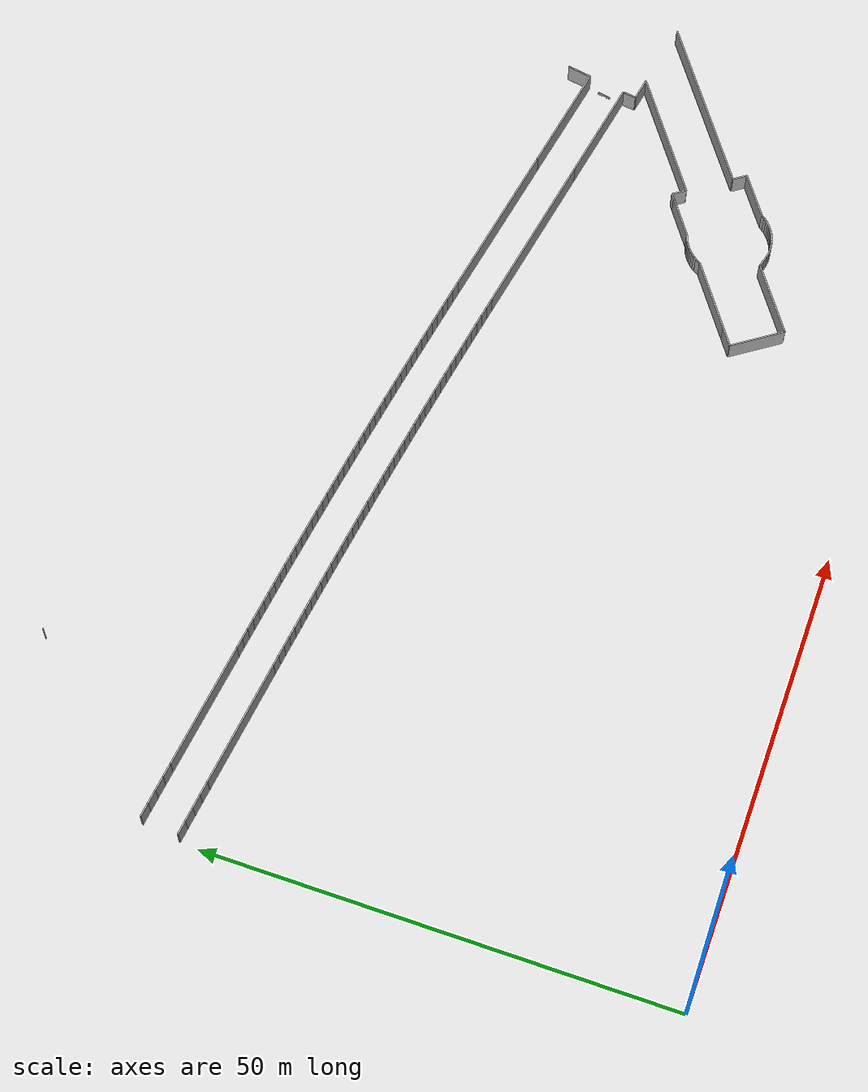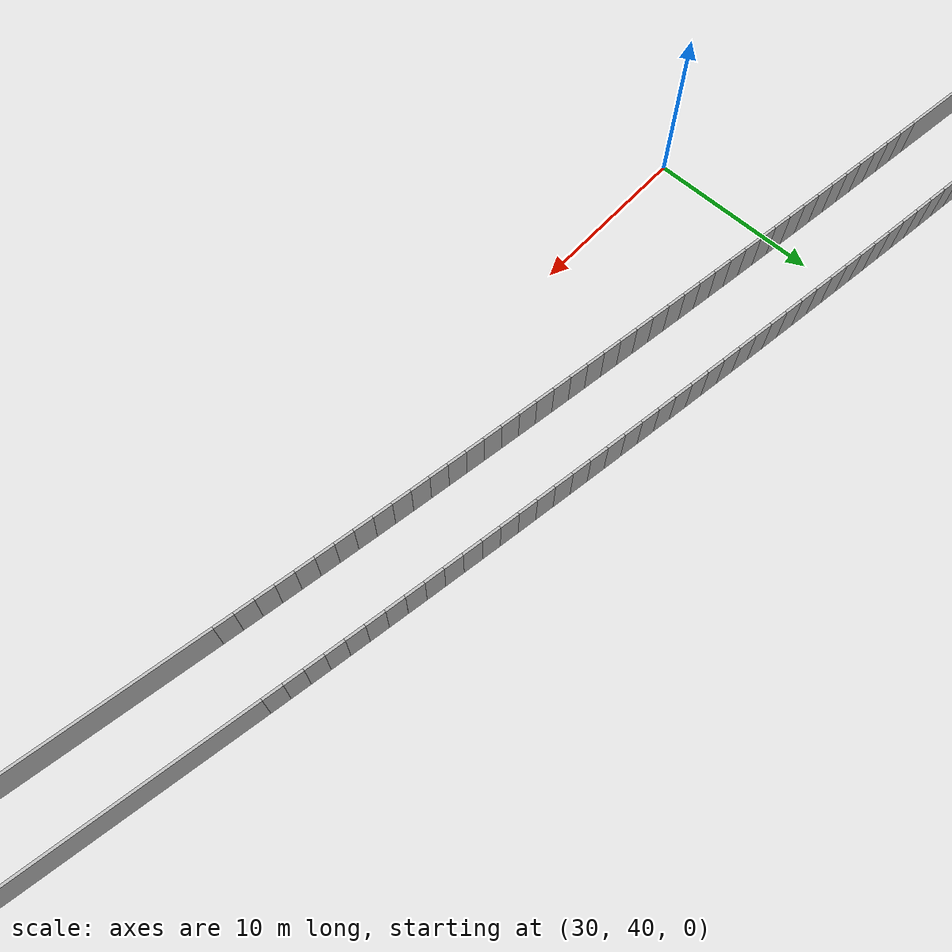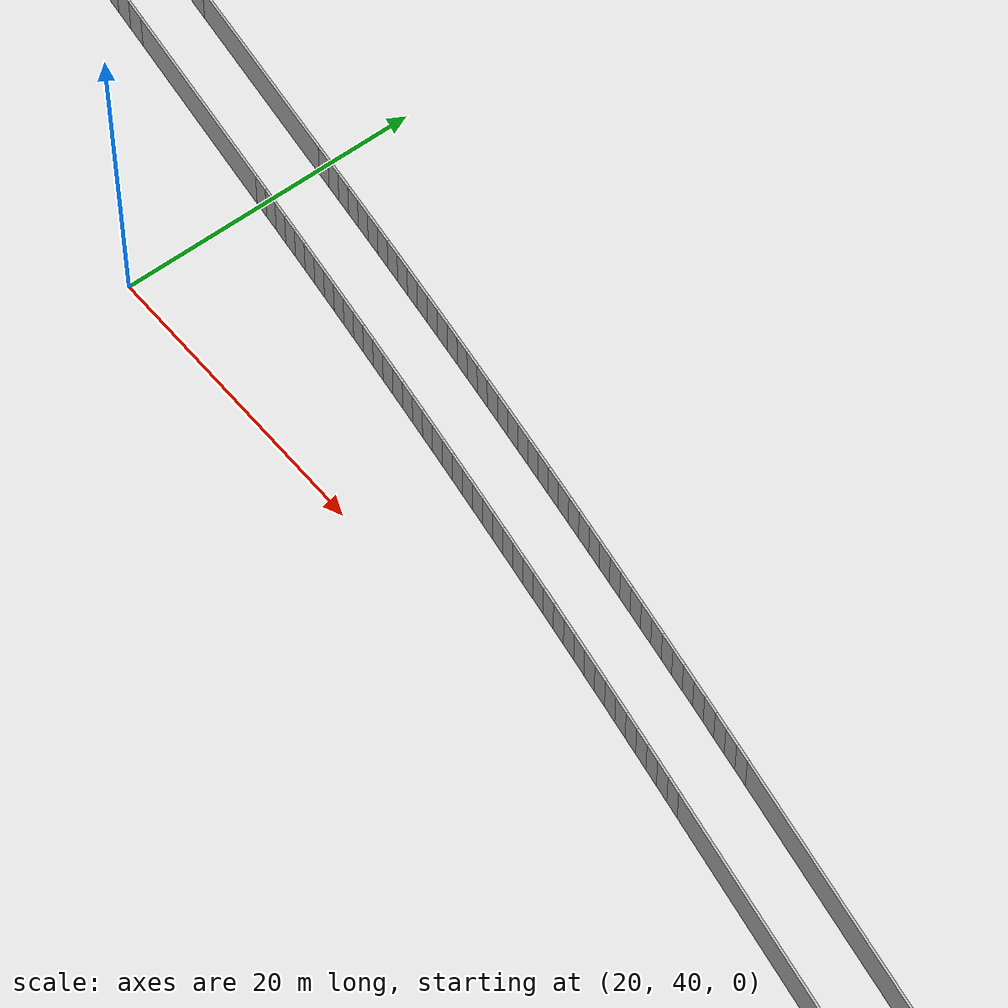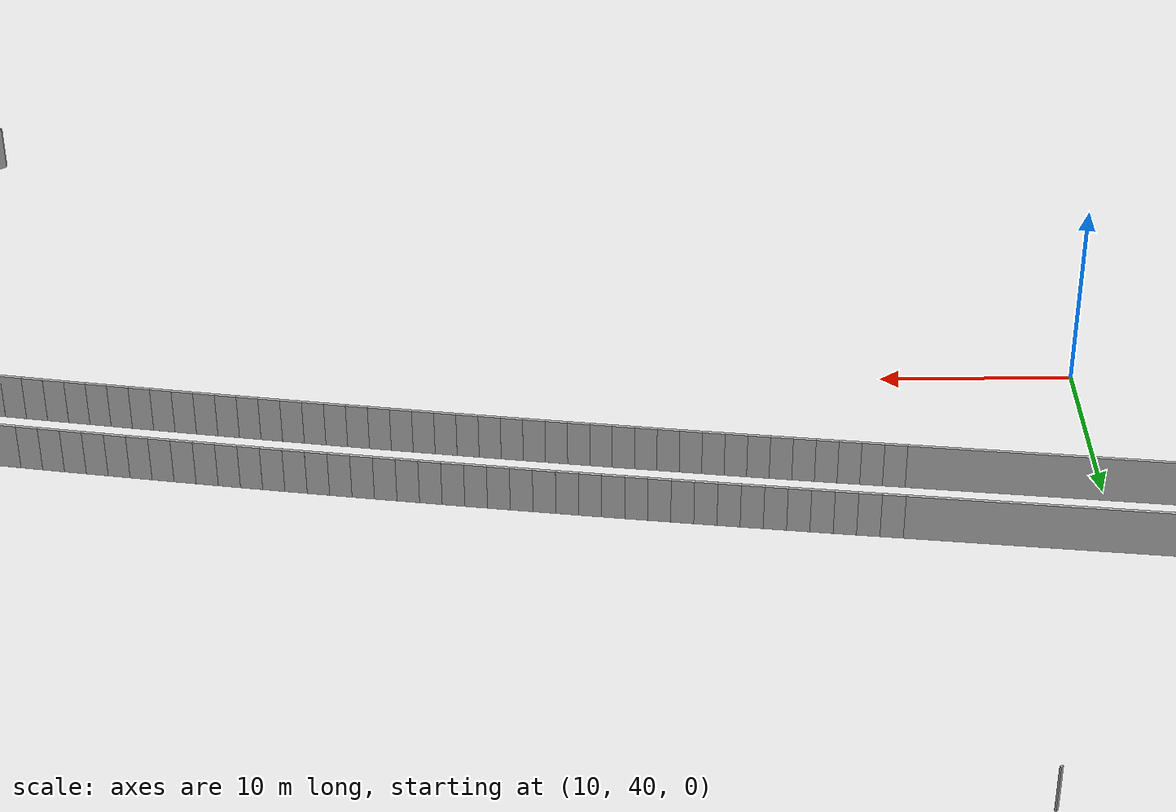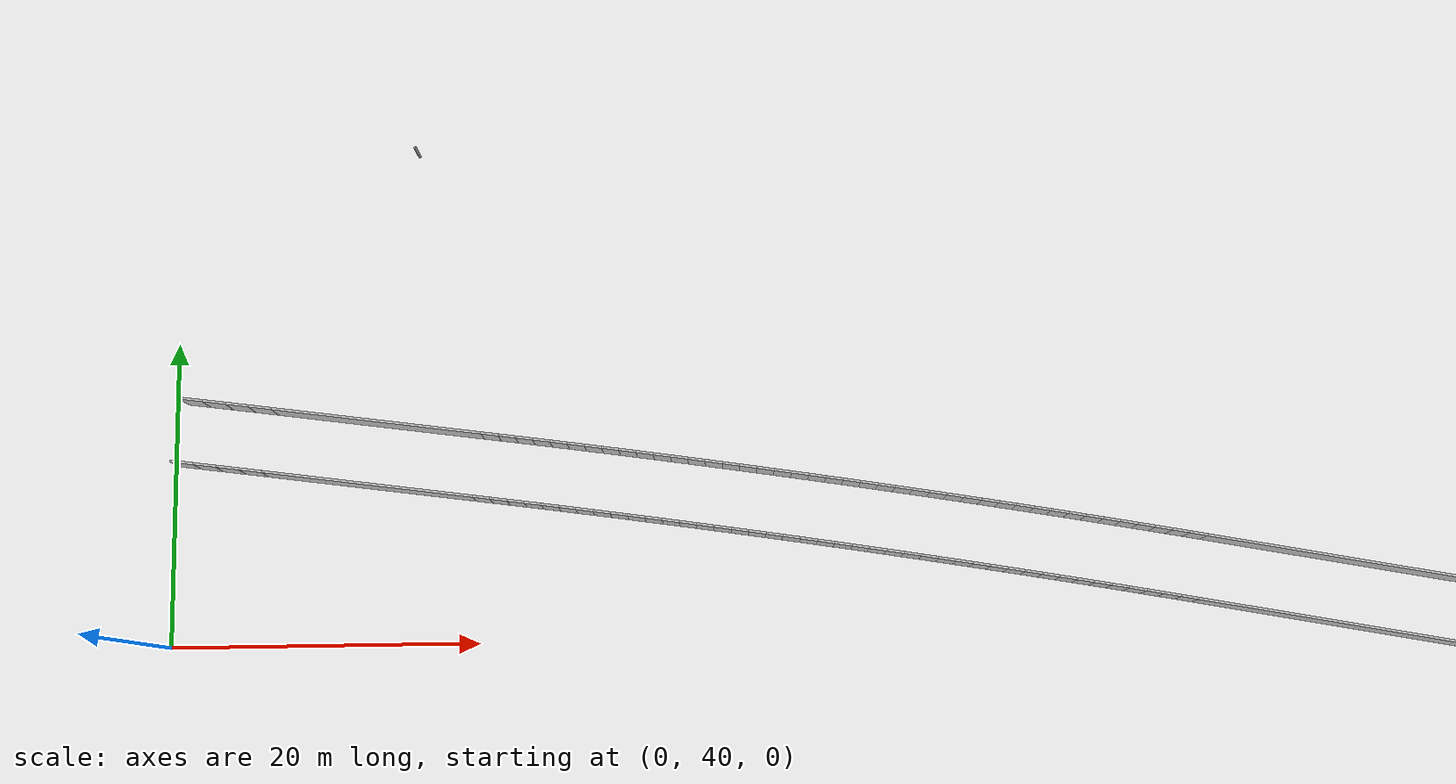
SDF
<?xml version="1.0" ?>
<sdf version="1.6">
  <model name="sps_1323">
    <pose frame="">0 0 0 0 -0 0</pose>
    <static>1</static>
    <self_collide>0</self_collide>
    <allow_auto_disable>0</allow_auto_disable>
    <link name="Wall66">
      <kinematic>0</kinematic>
      <gravity>1</gravity>
      <self_collide>0</self_collide>
      <collision name="collision">
        <geometry>
          <box>
            <size>2.18574 0.15 2.5</size>
          </box>
        </geometry>
        <pose frame="">0 0 0 0 -0 0</pose>
      </collision>
      <visual name="visual">
        <geometry>
          <box>
            <size>2.18574 0.15 2.5</size>
          </box>
        </geometry>
        <pose frame="">0 0 0 0 -0 0</pose>
        <cast_shadows>1</cast_shadows>
        <transparency>0.0</transparency>
      </visual>
      <pose frame="">70.1644 17.2707 1.25 0 -0 0.605917</pose>
    </link>
    <link name="Wall67">
      <kinematic>0</kinematic>
      <gravity>1</gravity>
      <self_collide>0</self_collide>
      <collision name="collision">
        <geometry>
          <box>
            <size>8.16413 0.15 2.5</size>
          </box>
        </geometry>
        <pose frame="">0 0 0 0 -0 0</pose>
      </collision>
      <visual name="visual">
        <geometry>
          <box>
            <size>8.16413 0.15 2.5</size>
          </box>
        </geometry>
        <pose frame="">0 0 0 0 -0 0</pose>
        <cast_shadows>1</cast_shadows>
        <transparency>0.0</transparency>
      </visual>
      <pose frame="">74.4181 20.2179 1.25 0 -0 0.605917</pose>
    </link>
    <link name="Wall68">
      <kinematic>0</kinematic>
      <gravity>1</gravity>
      <self_collide>0</self_collide>
      <collision name="collision">
        <geometry>
          <box>
            <size>2.66015 0.15 2.5</size>
          </box>
        </geometry>
        <pose frame="">0 0 0 0 -0 0</pose>
      </collision>
      <visual name="visual">
        <geometry>
          <box>
            <size>2.66015 0.15 2.5</size>
          </box>
        </geometry>
        <pose frame="">0 0 0 0 -0 0</pose>
        <cast_shadows>1</cast_shadows>
        <transparency>0.0</transparency>
      </visual>
      <pose frame="">96.7183 42.2026 1.25 0 -0 1.39135</pose>
    </link>
    <link name="Wall143">
      <kinematic>0</kinematic>
      <gravity>1</gravity>
      <self_collide>0</self_collide>
      <collision name="collision">
        <geometry>
          <box>
            <size>1.49983 0.15 2.5</size>
          </box>
        </geometry>
        <pose frame="">0 0 0 0 -0 0</pose>
      </collision>
      <visual name="visual">
        <geometry>
          <box>
            <size>1.49983 0.15 2.5</size>
          </box>
        </geometry>
        <pose frame="">0 0 0 0 -0 0</pose>
        <cast_shadows>1</cast_shadows>
        <transparency>0.0</transparency>
      </visual>
      <pose frame="">95.6082 36.0828 1.25 0 -0 1.39168</pose>
    </link>
    <link name="Wall144">
      <kinematic>0</kinematic>
      <gravity>1</gravity>
      <self_collide>0</self_collide>
      <collision name="collision">
        <geometry>
          <box>
            <size>11.4563 0.15 2.5</size>
          </box>
        </geometry>
        <pose frame="">0 0 0 0 -0 0</pose>
      </collision>
      <visual name="visual">
        <geometry>
          <box>
            <size>11.4563 0.15 2.5</size>
          </box>
        </geometry>
        <pose frame="">0 0 0 0 -0 0</pose>
        <cast_shadows>1</cast_shadows>
        <transparency>0.0</transparency>
      </visual>
      <pose frame="">90.1056 37.8428 1.25 0 -0 2.9622</pose>
    </link>
    <link name="Wall145">
      <kinematic>0</kinematic>
      <gravity>1</gravity>
      <self_collide>0</self_collide>
      <collision name="collision">
        <geometry>
          <box>
            <size>18.5098 0.15 2.5</size>
          </box>
        </geometry>
        <pose frame="">0 0 0 0 -0 0</pose>
      </collision>
      <visual name="visual">
        <geometry>
          <box>
            <size>18.5098 0.15 2.5</size>
          </box>
        </geometry>
        <pose frame="">0 0 0 0 -0 0</pose>
        <cast_shadows>1</cast_shadows>
        <transparency>0.0</transparency>
      </visual>
      <pose frame="">75.3631 40.5163 1.25 0 -0 2.9622</pose>
    </link>
    <link name="Wall251">
      <kinematic>0</kinematic>
      <gravity>1</gravity>
      <self_collide>0</self_collide>
      <collision name="collision">
        <geometry>
          <box>
            <size>13.7265 0.15 2.5</size>
          </box>
        </geometry>
        <pose frame="">0 0 0 0 -0 0</pose>
      </collision>
      <visual name="visual">
        <geometry>
          <box>
            <size>13.7265 0.15 2.5</size>
          </box>
        </geometry>
        <pose frame="">0 0 0 0 -0 0</pose>
        <cast_shadows>1</cast_shadows>
        <transparency>0.0</transparency>
      </visual>
      <pose frame="">12.9153 50.2794 1.25 0 0 -0.130471</pose>
    </link>
    <link name="Wall252">
      <kinematic>0</kinematic>
      <gravity>1</gravity>
      <self_collide>0</self_collide>
      <collision name="collision">
        <geometry>
          <box>
            <size>6.10074 0.15 2.5</size>
          </box>
        </geometry>
        <pose frame="">0 0 0 0 -0 0</pose>
      </collision>
      <visual name="visual">
        <geometry>
          <box>
            <size>6.10074 0.15 2.5</size>
          </box>
        </geometry>
        <pose frame="">0 0 0 0 -0 0</pose>
        <cast_shadows>1</cast_shadows>
        <transparency>0.0</transparency>
      </visual>
      <pose frame="">71.0034 14.141 1.25 0 -0 2.17674</pose>
    </link>
    <link name="Wall253">
      <kinematic>0</kinematic>
      <gravity>1</gravity>
      <self_collide>0</self_collide>
      <collision name="collision">
        <geometry>
          <box>
            <size>14.6083 0.15 2.5</size>
          </box>
        </geometry>
        <pose frame="">0 0 0 0 -0 0</pose>
      </collision>
      <visual name="visual">
        <geometry>
          <box>
            <size>14.6083 0.15 2.5</size>
          </box>
        </geometry>
        <pose frame="">0 0 0 0 -0 0</pose>
        <cast_shadows>1</cast_shadows>
        <transparency>0.0</transparency>
      </visual>
      <pose frame="">91.9368 30.7295 1.25 0 -0 0.607546</pose>
    </link>
    <link name="Wall254">
      <kinematic>0</kinematic>
      <gravity>1</gravity>
      <self_collide>0</self_collide>
      <collision name="collision">
        <geometry>
          <box>
            <size>19.912 0.15 2.5</size>
          </box>
        </geometry>
        <pose frame="">0 0 0 0 -0 0</pose>
      </collision>
      <visual name="visual">
        <geometry>
          <box>
            <size>19.912 0.15 2.5</size>
          </box>
        </geometry>
        <pose frame="">0 0 0 0 -0 0</pose>
        <cast_shadows>1</cast_shadows>
        <transparency>0.0</transparency>
      </visual>
      <pose frame="">97.1357 27.8817 1.25 0 0 -2.53463</pose>
    </link>
    <link name="Wall316">
      <kinematic>0</kinematic>
      <gravity>1</gravity>
      <self_collide>0</self_collide>
      <collision name="collision">
        <geometry>
          <box>
            <size>5.1925 0.15 2.5</size>
          </box>
        </geometry>
        <pose frame="">0 0 0 0 -0 0</pose>
      </collision>
      <visual name="visual">
        <geometry>
          <box>
            <size>5.1925 0.15 2.5</size>
          </box>
        </geometry>
        <pose frame="">0 0 0 0 -0 0</pose>
        <cast_shadows>1</cast_shadows>
        <transparency>0.0</transparency>
      </visual>
      <pose frame="">87.7356 19.4094 1.25 0 0 -2.53563</pose>
    </link>
    <link name="Wall317">
      <kinematic>0</kinematic>
      <gravity>1</gravity>
      <self_collide>0</self_collide>
      <collision name="collision">
        <geometry>
          <box>
            <size>2.4993 0.15 2.5</size>
          </box>
        </geometry>
        <pose frame="">0 0 0 0 -0 0</pose>
      </collision>
      <visual name="visual">
        <geometry>
          <box>
            <size>2.4993 0.15 2.5</size>
          </box>
        </geometry>
        <pose frame="">0 0 0 0 -0 0</pose>
        <cast_shadows>1</cast_shadows>
        <transparency>0.0</transparency>
      </visual>
      <pose frame="">96.7042 35.122 1.25 0 -0 2.96229</pose>
    </link>
    <link name="Wall381">
      <kinematic>0</kinematic>
      <gravity>1</gravity>
      <self_collide>0</self_collide>
      <collision name="collision">
        <geometry>
          <box>
            <size>8.38171 0.15 2.5</size>
          </box>
        </geometry>
        <pose frame="">0 0 0 0 -0 0</pose>
      </collision>
      <visual name="visual">
        <geometry>
          <box>
            <size>8.38171 0.15 2.5</size>
          </box>
        </geometry>
        <pose frame="">0 0 0 0 -0 0</pose>
        <cast_shadows>1</cast_shadows>
        <transparency>0.0</transparency>
      </visual>
      <pose frame="">76.1852 14.0209 1.25 0 0 -2.53555</pose>
    </link>
    <link name="Wall382">
      <kinematic>0</kinematic>
      <gravity>1</gravity>
      <self_collide>0</self_collide>
      <collision name="collision">
        <geometry>
          <box>
            <size>17.7611 0.15 2.5</size>
          </box>
        </geometry>
        <pose frame="">0 0 0 0 -0 0</pose>
      </collision>
      <visual name="visual">
        <geometry>
          <box>
            <size>17.7611 0.15 2.5</size>
          </box>
        </geometry>
        <pose frame="">0 0 0 0 -0 0</pose>
        <cast_shadows>1</cast_shadows>
        <transparency>0.0</transparency>
      </visual>
      <pose frame="">75.7314 44.6568 1.25 0 0 -0.179402</pose>
    </link>
    <link name="Wall383">
      <kinematic>0</kinematic>
      <gravity>1</gravity>
      <self_collide>0</self_collide>
      <collision name="collision">
        <geometry>
          <box>
            <size>12.2073 0.15 2.5</size>
          </box>
        </geometry>
        <pose frame="">0 0 0 0 -0 0</pose>
      </collision>
      <visual name="visual">
        <geometry>
          <box>
            <size>12.2073 0.15 2.5</size>
          </box>
        </geometry>
        <pose frame="">0 0 0 0 -0 0</pose>
        <cast_shadows>1</cast_shadows>
        <transparency>0.0</transparency>
      </visual>
      <pose frame="">90.4752 41.983 1.25 0 0 -0.179402</pose>
    </link>
    <link name="Wall475">
      <kinematic>0</kinematic>
      <gravity>1</gravity>
      <self_collide>0</self_collide>
      <collision name="collision">
        <geometry>
          <box>
            <size>1.6001 0.15 2.5</size>
          </box>
        </geometry>
        <pose frame="">0 0 0 0 -0 0</pose>
      </collision>
      <visual name="visual">
        <geometry>
          <box>
            <size>1.6001 0.15 2.5</size>
          </box>
        </geometry>
        <pose frame="">0 0 0 0 -0 0</pose>
        <cast_shadows>1</cast_shadows>
        <transparency>0.0</transparency>
      </visual>
      <pose frame="">85.484 27.2175 1.25 0 0 -0.964808</pose>
    </link>
    <link name="Wall476">
      <kinematic>0</kinematic>
      <gravity>1</gravity>
      <self_collide>0</self_collide>
      <collision name="collision">
        <geometry>
          <box>
            <size>1.60009 0.15 2.5</size>
          </box>
        </geometry>
        <pose frame="">0 0 0 0 -0 0</pose>
      </collision>
      <visual name="visual">
        <geometry>
          <box>
            <size>1.60009 0.15 2.5</size>
          </box>
        </geometry>
        <pose frame="">0 0 0 0 -0 0</pose>
        <cast_shadows>1</cast_shadows>
        <transparency>0.0</transparency>
      </visual>
      <pose frame="">89.4138 21.5456 1.25 0 0 -0.964617</pose>
    </link>
    <link name="Wall566">
      <kinematic>0</kinematic>
      <gravity>1</gravity>
      <self_collide>0</self_collide>
      <collision name="collision">
        <geometry>
          <box>
            <size>13.7167 0.15 2.5</size>
          </box>
        </geometry>
        <pose frame="">0 0 0 0 -0 0</pose>
      </collision>
      <visual name="visual">
        <geometry>
          <box>
            <size>13.7167 0.15 2.5</size>
          </box>
        </geometry>
        <pose frame="">0 0 0 0 -0 0</pose>
        <cast_shadows>1</cast_shadows>
        <transparency>0.0</transparency>
      </visual>
      <pose frame="">13.4524 54.3841 1.25 0 0 -0.130429</pose>
    </link>
    <link name="Wall567">
      <kinematic>0</kinematic>
      <gravity>1</gravity>
      <self_collide>0</self_collide>
      <collision name="collision">
        <geometry>
          <box>
            <size>0.610231 0.15 2.5</size>
          </box>
        </geometry>
        <pose frame="">0 0 0 0 -0 0</pose>
      </collision>
      <visual name="visual">
        <geometry>
          <box>
            <size>0.610231 0.15 2.5</size>
          </box>
        </geometry>
        <pose frame="">0 0 0 0 -0 0</pose>
        <cast_shadows>1</cast_shadows>
        <transparency>0.0</transparency>
      </visual>
      <pose frame="">77.9307 22.8042 1.25 0 0 -2.11204</pose>
    </link>
    <link name="Wall568">
      <kinematic>0</kinematic>
      <gravity>1</gravity>
      <self_collide>0</self_collide>
      <collision name="collision">
        <geometry>
          <box>
            <size>0.774105 0.15 2.5</size>
          </box>
        </geometry>
        <pose frame="">0 0 0 0 -0 0</pose>
      </collision>
      <visual name="visual">
        <geometry>
          <box>
            <size>0.774105 0.15 2.5</size>
          </box>
        </geometry>
        <pose frame="">0 0 0 0 -0 0</pose>
        <cast_shadows>1</cast_shadows>
        <transparency>0.0</transparency>
      </visual>
      <pose frame="">80.2564 24.7115 1.25 0 -0 0.349081</pose>
    </link>
    <link name="Wall569">
      <kinematic>0</kinematic>
      <gravity>1</gravity>
      <self_collide>0</self_collide>
      <collision name="collision">
        <geometry>
          <box>
            <size>4.67159 0.15 2.5</size>
          </box>
        </geometry>
        <pose frame="">0 0 0 0 -0 0</pose>
      </collision>
      <visual name="visual">
        <geometry>
          <box>
            <size>4.67159 0.15 2.5</size>
          </box>
        </geometry>
        <pose frame="">0 0 0 0 -0 0</pose>
        <cast_shadows>1</cast_shadows>
        <transparency>0.0</transparency>
      </visual>
      <pose frame="">82.5448 26.1673 1.25 0 -0 0.602372</pose>
    </link>
    <link name="Wall570">
      <kinematic>0</kinematic>
      <gravity>1</gravity>
      <self_collide>0</self_collide>
      <collision name="collision">
        <geometry>
          <box>
            <size>0.678206 0.15 2.5</size>
          </box>
        </geometry>
        <pose frame="">0 0 0 0 -0 0</pose>
      </collision>
      <visual name="visual">
        <geometry>
          <box>
            <size>0.678206 0.15 2.5</size>
          </box>
        </geometry>
        <pose frame="">0 0 0 0 -0 0</pose>
        <cast_shadows>1</cast_shadows>
        <transparency>0.0</transparency>
      </visual>
      <pose frame="">84.7489 27.6829 1.25 0 -0 0.602372</pose>
    </link>
    <link name="Wall646">
      <kinematic>0</kinematic>
      <gravity>1</gravity>
      <self_collide>0</self_collide>
      <collision name="collision">
        <geometry>
          <box>
            <size>0.100699 0.15 2.5</size>
          </box>
        </geometry>
        <pose frame="">0 0 0 0 -0 0</pose>
      </collision>
      <visual name="visual">
        <geometry>
          <box>
            <size>0.100699 0.15 2.5</size>
          </box>
        </geometry>
        <pose frame="">0 0 0 0 -0 0</pose>
        <cast_shadows>1</cast_shadows>
        <transparency>0.0</transparency>
      </visual>
      <pose frame="">15.8079 72.6316 1.25 0 -0 2.34205</pose>
    </link>
    <link name="Wall2821">
      <kinematic>0</kinematic>
      <gravity>1</gravity>
      <self_collide>0</self_collide>
      <collision name="collision">
        <geometry>
          <box>
            <size>1.49673 0.15 2.5</size>
          </box>
        </geometry>
        <pose frame="">0 0 0 0 -0 0</pose>
      </collision>
      <visual name="visual">
        <geometry>
          <box>
            <size>1.49673 0.15 2.5</size>
          </box>
        </geometry>
        <pose frame="">0 0 0 0 -0 0</pose>
        <cast_shadows>1</cast_shadows>
        <transparency>0.0</transparency>
      </visual>
      <pose frame="">5.36843 51.2697 1.25 0 -0 3.0111</pose>
    </link>
    <link name="Wall2822">
      <kinematic>0</kinematic>
      <gravity>1</gravity>
      <self_collide>0</self_collide>
      <collision name="collision">
        <geometry>
          <box>
            <size>1.4964 0.15 2.5</size>
          </box>
        </geometry>
        <pose frame="">0 0 0 0 -0 0</pose>
      </collision>
      <visual name="visual">
        <geometry>
          <box>
            <size>1.4964 0.15 2.5</size>
          </box>
        </geometry>
        <pose frame="">0 0 0 0 -0 0</pose>
        <cast_shadows>1</cast_shadows>
        <transparency>0.0</transparency>
      </visual>
      <pose frame="">3.88445 51.4634 1.25 0 -0 3.01251</pose>
    </link>
    <link name="Wall2823">
      <kinematic>0</kinematic>
      <gravity>1</gravity>
      <self_collide>0</self_collide>
      <collision name="collision">
        <geometry>
          <box>
            <size>1.49657 0.15 2.5</size>
          </box>
        </geometry>
        <pose frame="">0 0 0 0 -0 0</pose>
      </collision>
      <visual name="visual">
        <geometry>
          <box>
            <size>1.49657 0.15 2.5</size>
          </box>
        </geometry>
        <pose frame="">0 0 0 0 -0 0</pose>
        <cast_shadows>1</cast_shadows>
        <transparency>0.0</transparency>
      </visual>
      <pose frame="">2.40026 51.6548 1.25 0 -0 3.01417</pose>
    </link>
    <link name="Wall2824">
      <kinematic>0</kinematic>
      <gravity>1</gravity>
      <self_collide>0</self_collide>
      <collision name="collision">
        <geometry>
          <box>
            <size>1.49637 0.15 2.5</size>
          </box>
        </geometry>
        <pose frame="">0 0 0 0 -0 0</pose>
      </collision>
      <visual name="visual">
        <geometry>
          <box>
            <size>1.49637 0.15 2.5</size>
          </box>
        </geometry>
        <pose frame="">0 0 0 0 -0 0</pose>
        <cast_shadows>1</cast_shadows>
        <transparency>0.0</transparency>
      </visual>
      <pose frame="">0.915763 51.8437 1.25 0 -0 3.01588</pose>
    </link>
    <link name="Wall3459">
      <kinematic>0</kinematic>
      <gravity>1</gravity>
      <self_collide>0</self_collide>
      <collision name="collision">
        <geometry>
          <box>
            <size>1.12144 0.15 2.5</size>
          </box>
        </geometry>
        <pose frame="">0 0 0 0 -0 0</pose>
      </collision>
      <visual name="visual">
        <geometry>
          <box>
            <size>1.12144 0.15 2.5</size>
          </box>
        </geometry>
        <pose frame="">0 0 0 0 -0 0</pose>
        <cast_shadows>1</cast_shadows>
        <transparency>0.0</transparency>
      </visual>
      <pose frame="">65.7049 42.2672 1.25 0 -0 2.96317</pose>
    </link>
    <link name="Wall3460">
      <kinematic>0</kinematic>
      <gravity>1</gravity>
      <self_collide>0</self_collide>
      <collision name="collision">
        <geometry>
          <box>
            <size>1.12127 0.15 2.5</size>
          </box>
        </geometry>
        <pose frame="">0 0 0 0 -0 0</pose>
      </collision>
      <visual name="visual">
        <geometry>
          <box>
            <size>1.12127 0.15 2.5</size>
          </box>
        </geometry>
        <pose frame="">0 0 0 0 -0 0</pose>
        <cast_shadows>1</cast_shadows>
        <transparency>0.0</transparency>
      </visual>
      <pose frame="">64.6012 42.4654 1.25 0 -0 2.96463</pose>
    </link>
    <link name="Wall3461">
      <kinematic>0</kinematic>
      <gravity>1</gravity>
      <self_collide>0</self_collide>
      <collision name="collision">
        <geometry>
          <box>
            <size>1.1213 0.15 2.5</size>
          </box>
        </geometry>
        <pose frame="">0 0 0 0 -0 0</pose>
      </collision>
      <visual name="visual">
        <geometry>
          <box>
            <size>1.1213 0.15 2.5</size>
          </box>
        </geometry>
        <pose frame="">0 0 0 0 -0 0</pose>
        <cast_shadows>1</cast_shadows>
        <transparency>0.0</transparency>
      </visual>
      <pose frame="">63.4973 42.6622 1.25 0 -0 2.96574</pose>
    </link>
    <link name="Wall3462">
      <kinematic>0</kinematic>
      <gravity>1</gravity>
      <self_collide>0</self_collide>
      <collision name="collision">
        <geometry>
          <box>
            <size>1.12152 0.15 2.5</size>
          </box>
        </geometry>
        <pose frame="">0 0 0 0 -0 0</pose>
      </collision>
      <visual name="visual">
        <geometry>
          <box>
            <size>1.12152 0.15 2.5</size>
          </box>
        </geometry>
        <pose frame="">0 0 0 0 -0 0</pose>
        <cast_shadows>1</cast_shadows>
        <transparency>0.0</transparency>
      </visual>
      <pose frame="">62.3931 42.8578 1.25 0 -0 2.96683</pose>
    </link>
    <link name="Wall3463">
      <kinematic>0</kinematic>
      <gravity>1</gravity>
      <self_collide>0</self_collide>
      <collision name="collision">
        <geometry>
          <box>
            <size>1.12145 0.15 2.5</size>
          </box>
        </geometry>
        <pose frame="">0 0 0 0 -0 0</pose>
      </collision>
      <visual name="visual">
        <geometry>
          <box>
            <size>1.12145 0.15 2.5</size>
          </box>
        </geometry>
        <pose frame="">0 0 0 0 -0 0</pose>
        <cast_shadows>1</cast_shadows>
        <transparency>0.0</transparency>
      </visual>
      <pose frame="">61.2885 43.0521 1.25 0 -0 2.96809</pose>
    </link>
    <link name="Wall3464">
      <kinematic>0</kinematic>
      <gravity>1</gravity>
      <self_collide>0</self_collide>
      <collision name="collision">
        <geometry>
          <box>
            <size>1.12157 0.15 2.5</size>
          </box>
        </geometry>
        <pose frame="">0 0 0 0 -0 0</pose>
      </collision>
      <visual name="visual">
        <geometry>
          <box>
            <size>1.12157 0.15 2.5</size>
          </box>
        </geometry>
        <pose frame="">0 0 0 0 -0 0</pose>
        <cast_shadows>1</cast_shadows>
        <transparency>0.0</transparency>
      </visual>
      <pose frame="">60.1837 43.245 1.25 0 -0 2.96938</pose>
    </link>
    <link name="Wall3465">
      <kinematic>0</kinematic>
      <gravity>1</gravity>
      <self_collide>0</self_collide>
      <collision name="collision">
        <geometry>
          <box>
            <size>1.12133 0.15 2.5</size>
          </box>
        </geometry>
        <pose frame="">0 0 0 0 -0 0</pose>
      </collision>
      <visual name="visual">
        <geometry>
          <box>
            <size>1.12133 0.15 2.5</size>
          </box>
        </geometry>
        <pose frame="">0 0 0 0 -0 0</pose>
        <cast_shadows>1</cast_shadows>
        <transparency>0.0</transparency>
      </visual>
      <pose frame="">59.0788 43.4365 1.25 0 -0 2.97061</pose>
    </link>
    <link name="Wall3466">
      <kinematic>0</kinematic>
      <gravity>1</gravity>
      <self_collide>0</self_collide>
      <collision name="collision">
        <geometry>
          <box>
            <size>1.12141 0.15 2.5</size>
          </box>
        </geometry>
        <pose frame="">0 0 0 0 -0 0</pose>
      </collision>
      <visual name="visual">
        <geometry>
          <box>
            <size>1.12141 0.15 2.5</size>
          </box>
        </geometry>
        <pose frame="">0 0 0 0 -0 0</pose>
        <cast_shadows>1</cast_shadows>
        <transparency>0.0</transparency>
      </visual>
      <pose frame="">57.9737 43.6268 1.25 0 -0 2.9715</pose>
    </link>
    <link name="Wall3467">
      <kinematic>0</kinematic>
      <gravity>1</gravity>
      <self_collide>0</self_collide>
      <collision name="collision">
        <geometry>
          <box>
            <size>1.12131 0.15 2.5</size>
          </box>
        </geometry>
        <pose frame="">0 0 0 0 -0 0</pose>
      </collision>
      <visual name="visual">
        <geometry>
          <box>
            <size>1.12131 0.15 2.5</size>
          </box>
        </geometry>
        <pose frame="">0 0 0 0 -0 0</pose>
        <cast_shadows>1</cast_shadows>
        <transparency>0.0</transparency>
      </visual>
      <pose frame="">56.8683 43.8158 1.25 0 -0 2.97298</pose>
    </link>
    <link name="Wall3468">
      <kinematic>0</kinematic>
      <gravity>1</gravity>
      <self_collide>0</self_collide>
      <collision name="collision">
        <geometry>
          <box>
            <size>1.1213 0.15 2.5</size>
          </box>
        </geometry>
        <pose frame="">0 0 0 0 -0 0</pose>
      </collision>
      <visual name="visual">
        <geometry>
          <box>
            <size>1.1213 0.15 2.5</size>
          </box>
        </geometry>
        <pose frame="">0 0 0 0 -0 0</pose>
        <cast_shadows>1</cast_shadows>
        <transparency>0.0</transparency>
      </visual>
      <pose frame="">55.7628 44.0034 1.25 0 -0 2.97403</pose>
    </link>
    <link name="Wall3469">
      <kinematic>0</kinematic>
      <gravity>1</gravity>
      <self_collide>0</self_collide>
      <collision name="collision">
        <geometry>
          <box>
            <size>1.12124 0.15 2.5</size>
          </box>
        </geometry>
        <pose frame="">0 0 0 0 -0 0</pose>
      </collision>
      <visual name="visual">
        <geometry>
          <box>
            <size>1.12124 0.15 2.5</size>
          </box>
        </geometry>
        <pose frame="">0 0 0 0 -0 0</pose>
        <cast_shadows>1</cast_shadows>
        <transparency>0.0</transparency>
      </visual>
      <pose frame="">54.6572 44.1897 1.25 0 -0 2.97529</pose>
    </link>
    <link name="Wall3470">
      <kinematic>0</kinematic>
      <gravity>1</gravity>
      <self_collide>0</self_collide>
      <collision name="collision">
        <geometry>
          <box>
            <size>1.12146 0.15 2.5</size>
          </box>
        </geometry>
        <pose frame="">0 0 0 0 -0 0</pose>
      </collision>
      <visual name="visual">
        <geometry>
          <box>
            <size>1.12146 0.15 2.5</size>
          </box>
        </geometry>
        <pose frame="">0 0 0 0 -0 0</pose>
        <cast_shadows>1</cast_shadows>
        <transparency>0.0</transparency>
      </visual>
      <pose frame="">53.5512 44.3747 1.25 0 -0 2.97643</pose>
    </link>
    <link name="Wall3471">
      <kinematic>0</kinematic>
      <gravity>1</gravity>
      <self_collide>0</self_collide>
      <collision name="collision">
        <geometry>
          <box>
            <size>1.12142 0.15 2.5</size>
          </box>
        </geometry>
        <pose frame="">0 0 0 0 -0 0</pose>
      </collision>
      <visual name="visual">
        <geometry>
          <box>
            <size>1.12142 0.15 2.5</size>
          </box>
        </geometry>
        <pose frame="">0 0 0 0 -0 0</pose>
        <cast_shadows>1</cast_shadows>
        <transparency>0.0</transparency>
      </visual>
      <pose frame="">52.4449 44.5584 1.25 0 -0 2.97763</pose>
    </link>
    <link name="Wall3472">
      <kinematic>0</kinematic>
      <gravity>1</gravity>
      <self_collide>0</self_collide>
      <collision name="collision">
        <geometry>
          <box>
            <size>1.12128 0.15 2.5</size>
          </box>
        </geometry>
        <pose frame="">0 0 0 0 -0 0</pose>
      </collision>
      <visual name="visual">
        <geometry>
          <box>
            <size>1.12128 0.15 2.5</size>
          </box>
        </geometry>
        <pose frame="">0 0 0 0 -0 0</pose>
        <cast_shadows>1</cast_shadows>
        <transparency>0.0</transparency>
      </visual>
      <pose frame="">51.3385 44.7408 1.25 0 -0 2.97877</pose>
    </link>
    <link name="Wall3473">
      <kinematic>0</kinematic>
      <gravity>1</gravity>
      <self_collide>0</self_collide>
      <collision name="collision">
        <geometry>
          <box>
            <size>1.12142 0.15 2.5</size>
          </box>
        </geometry>
        <pose frame="">0 0 0 0 -0 0</pose>
      </collision>
      <visual name="visual">
        <geometry>
          <box>
            <size>1.12142 0.15 2.5</size>
          </box>
        </geometry>
        <pose frame="">0 0 0 0 -0 0</pose>
        <cast_shadows>1</cast_shadows>
        <transparency>0.0</transparency>
      </visual>
      <pose frame="">50.2318 44.9219 1.25 0 -0 2.98001</pose>
    </link>
    <link name="Wall3474">
      <kinematic>0</kinematic>
      <gravity>1</gravity>
      <self_collide>0</self_collide>
      <collision name="collision">
        <geometry>
          <box>
            <size>1.12141 0.15 2.5</size>
          </box>
        </geometry>
        <pose frame="">0 0 0 0 -0 0</pose>
      </collision>
      <visual name="visual">
        <geometry>
          <box>
            <size>1.12141 0.15 2.5</size>
          </box>
        </geometry>
        <pose frame="">0 0 0 0 -0 0</pose>
        <cast_shadows>1</cast_shadows>
        <transparency>0.0</transparency>
      </visual>
      <pose frame="">49.1249 45.1017 1.25 0 -0 2.98111</pose>
    </link>
    <link name="Wall3475">
      <kinematic>0</kinematic>
      <gravity>1</gravity>
      <self_collide>0</self_collide>
      <collision name="collision">
        <geometry>
          <box>
            <size>1.12136 0.15 2.5</size>
          </box>
        </geometry>
        <pose frame="">0 0 0 0 -0 0</pose>
      </collision>
      <visual name="visual">
        <geometry>
          <box>
            <size>1.12136 0.15 2.5</size>
          </box>
        </geometry>
        <pose frame="">0 0 0 0 -0 0</pose>
        <cast_shadows>1</cast_shadows>
        <transparency>0.0</transparency>
      </visual>
      <pose frame="">48.0178 45.2802 1.25 0 -0 2.98237</pose>
    </link>
    <link name="Wall3476">
      <kinematic>0</kinematic>
      <gravity>1</gravity>
      <self_collide>0</self_collide>
      <collision name="collision">
        <geometry>
          <box>
            <size>1.12138 0.15 2.5</size>
          </box>
        </geometry>
        <pose frame="">0 0 0 0 -0 0</pose>
      </collision>
      <visual name="visual">
        <geometry>
          <box>
            <size>1.12138 0.15 2.5</size>
          </box>
        </geometry>
        <pose frame="">0 0 0 0 -0 0</pose>
        <cast_shadows>1</cast_shadows>
        <transparency>0.0</transparency>
      </visual>
      <pose frame="">46.9105 45.4573 1.25 0 -0 2.98364</pose>
    </link>
    <link name="Wall3477">
      <kinematic>0</kinematic>
      <gravity>1</gravity>
      <self_collide>0</self_collide>
      <collision name="collision">
        <geometry>
          <box>
            <size>1.12138 0.15 2.5</size>
          </box>
        </geometry>
        <pose frame="">0 0 0 0 -0 0</pose>
      </collision>
      <visual name="visual">
        <geometry>
          <box>
            <size>1.12138 0.15 2.5</size>
          </box>
        </geometry>
        <pose frame="">0 0 0 0 -0 0</pose>
        <cast_shadows>1</cast_shadows>
        <transparency>0.0</transparency>
      </visual>
      <pose frame="">45.803 45.6331 1.25 0 -0 2.98469</pose>
    </link>
    <link name="Wall3478">
      <kinematic>0</kinematic>
      <gravity>1</gravity>
      <self_collide>0</self_collide>
      <collision name="collision">
        <geometry>
          <box>
            <size>1.12136 0.15 2.5</size>
          </box>
        </geometry>
        <pose frame="">0 0 0 0 -0 0</pose>
      </collision>
      <visual name="visual">
        <geometry>
          <box>
            <size>1.12136 0.15 2.5</size>
          </box>
        </geometry>
        <pose frame="">0 0 0 0 -0 0</pose>
        <cast_shadows>1</cast_shadows>
        <transparency>0.0</transparency>
      </visual>
      <pose frame="">44.6953 45.8077 1.25 0 -0 2.98584</pose>
    </link>
    <link name="Wall3479">
      <kinematic>0</kinematic>
      <gravity>1</gravity>
      <self_collide>0</self_collide>
      <collision name="collision">
        <geometry>
          <box>
            <size>1.12131 0.15 2.5</size>
          </box>
        </geometry>
        <pose frame="">0 0 0 0 -0 0</pose>
      </collision>
      <visual name="visual">
        <geometry>
          <box>
            <size>1.12131 0.15 2.5</size>
          </box>
        </geometry>
        <pose frame="">0 0 0 0 -0 0</pose>
        <cast_shadows>1</cast_shadows>
        <transparency>0.0</transparency>
      </visual>
      <pose frame="">43.5875 45.9809 1.25 0 -0 2.98721</pose>
    </link>
    <link name="Wall3480">
      <kinematic>0</kinematic>
      <gravity>1</gravity>
      <self_collide>0</self_collide>
      <collision name="collision">
        <geometry>
          <box>
            <size>1.12139 0.15 2.5</size>
          </box>
        </geometry>
        <pose frame="">0 0 0 0 -0 0</pose>
      </collision>
      <visual name="visual">
        <geometry>
          <box>
            <size>1.12139 0.15 2.5</size>
          </box>
        </geometry>
        <pose frame="">0 0 0 0 -0 0</pose>
        <cast_shadows>1</cast_shadows>
        <transparency>0.0</transparency>
      </visual>
      <pose frame="">42.4794 46.1528 1.25 0 -0 2.98816</pose>
    </link>
    <link name="Wall3481">
      <kinematic>0</kinematic>
      <gravity>1</gravity>
      <self_collide>0</self_collide>
      <collision name="collision">
        <geometry>
          <box>
            <size>1.12133 0.15 2.5</size>
          </box>
        </geometry>
        <pose frame="">0 0 0 0 -0 0</pose>
      </collision>
      <visual name="visual">
        <geometry>
          <box>
            <size>1.12133 0.15 2.5</size>
          </box>
        </geometry>
        <pose frame="">0 0 0 0 -0 0</pose>
        <cast_shadows>1</cast_shadows>
        <transparency>0.0</transparency>
      </visual>
      <pose frame="">41.3711 46.3234 1.25 0 -0 2.98958</pose>
    </link>
    <link name="Wall3482">
      <kinematic>0</kinematic>
      <gravity>1</gravity>
      <self_collide>0</self_collide>
      <collision name="collision">
        <geometry>
          <box>
            <size>1.12134 0.15 2.5</size>
          </box>
        </geometry>
        <pose frame="">0 0 0 0 -0 0</pose>
      </collision>
      <visual name="visual">
        <geometry>
          <box>
            <size>1.12134 0.15 2.5</size>
          </box>
        </geometry>
        <pose frame="">0 0 0 0 -0 0</pose>
        <cast_shadows>1</cast_shadows>
        <transparency>0.0</transparency>
      </visual>
      <pose frame="">40.2626 46.4926 1.25 0 -0 2.99063</pose>
    </link>
    <link name="Wall3483">
      <kinematic>0</kinematic>
      <gravity>1</gravity>
      <self_collide>0</self_collide>
      <collision name="collision">
        <geometry>
          <box>
            <size>1.12157 0.15 2.5</size>
          </box>
        </geometry>
        <pose frame="">0 0 0 0 -0 0</pose>
      </collision>
      <visual name="visual">
        <geometry>
          <box>
            <size>1.12157 0.15 2.5</size>
          </box>
        </geometry>
        <pose frame="">0 0 0 0 -0 0</pose>
        <cast_shadows>1</cast_shadows>
        <transparency>0.0</transparency>
      </visual>
      <pose frame="">39.1538 46.6606 1.25 0 -0 2.99181</pose>
    </link>
    <link name="Wall3484">
      <kinematic>0</kinematic>
      <gravity>1</gravity>
      <self_collide>0</self_collide>
      <collision name="collision">
        <geometry>
          <box>
            <size>1.12137 0.15 2.5</size>
          </box>
        </geometry>
        <pose frame="">0 0 0 0 -0 0</pose>
      </collision>
      <visual name="visual">
        <geometry>
          <box>
            <size>1.12137 0.15 2.5</size>
          </box>
        </geometry>
        <pose frame="">0 0 0 0 -0 0</pose>
        <cast_shadows>1</cast_shadows>
        <transparency>0.0</transparency>
      </visual>
      <pose frame="">38.0448 46.8273 1.25 0 -0 2.993</pose>
    </link>
    <link name="Wall3485">
      <kinematic>0</kinematic>
      <gravity>1</gravity>
      <self_collide>0</self_collide>
      <collision name="collision">
        <geometry>
          <box>
            <size>1.12134 0.15 2.5</size>
          </box>
        </geometry>
        <pose frame="">0 0 0 0 -0 0</pose>
      </collision>
      <visual name="visual">
        <geometry>
          <box>
            <size>1.12134 0.15 2.5</size>
          </box>
        </geometry>
        <pose frame="">0 0 0 0 -0 0</pose>
        <cast_shadows>1</cast_shadows>
        <transparency>0.0</transparency>
      </visual>
      <pose frame="">36.9357 46.9926 1.25 0 -0 2.99426</pose>
    </link>
    <link name="Wall3486">
      <kinematic>0</kinematic>
      <gravity>1</gravity>
      <self_collide>0</self_collide>
      <collision name="collision">
        <geometry>
          <box>
            <size>1.1214 0.15 2.5</size>
          </box>
        </geometry>
        <pose frame="">0 0 0 0 -0 0</pose>
      </collision>
      <visual name="visual">
        <geometry>
          <box>
            <size>1.1214 0.15 2.5</size>
          </box>
        </geometry>
        <pose frame="">0 0 0 0 -0 0</pose>
        <cast_shadows>1</cast_shadows>
        <transparency>0.0</transparency>
      </visual>
      <pose frame="">35.8263 47.1566 1.25 0 -0 2.99537</pose>
    </link>
    <link name="Wall3487">
      <kinematic>0</kinematic>
      <gravity>1</gravity>
      <self_collide>0</self_collide>
      <collision name="collision">
        <geometry>
          <box>
            <size>1.12132 0.15 2.5</size>
          </box>
        </geometry>
        <pose frame="">0 0 0 0 -0 0</pose>
      </collision>
      <visual name="visual">
        <geometry>
          <box>
            <size>1.12132 0.15 2.5</size>
          </box>
        </geometry>
        <pose frame="">0 0 0 0 -0 0</pose>
        <cast_shadows>1</cast_shadows>
        <transparency>0.0</transparency>
      </visual>
      <pose frame="">34.7168 47.3193 1.25 0 -0 2.99662</pose>
    </link>
    <link name="Wall3488">
      <kinematic>0</kinematic>
      <gravity>1</gravity>
      <self_collide>0</self_collide>
      <collision name="collision">
        <geometry>
          <box>
            <size>1.12136 0.15 2.5</size>
          </box>
        </geometry>
        <pose frame="">0 0 0 0 -0 0</pose>
      </collision>
      <visual name="visual">
        <geometry>
          <box>
            <size>1.12136 0.15 2.5</size>
          </box>
        </geometry>
        <pose frame="">0 0 0 0 -0 0</pose>
        <cast_shadows>1</cast_shadows>
        <transparency>0.0</transparency>
      </visual>
      <pose frame="">33.6072 47.4806 1.25 0 -0 2.99789</pose>
    </link>
    <link name="Wall3489">
      <kinematic>0</kinematic>
      <gravity>1</gravity>
      <self_collide>0</self_collide>
      <collision name="collision">
        <geometry>
          <box>
            <size>1.12164 0.15 2.5</size>
          </box>
        </geometry>
        <pose frame="">0 0 0 0 -0 0</pose>
      </collision>
      <visual name="visual">
        <geometry>
          <box>
            <size>1.12164 0.15 2.5</size>
          </box>
        </geometry>
        <pose frame="">0 0 0 0 -0 0</pose>
        <cast_shadows>1</cast_shadows>
        <transparency>0.0</transparency>
      </visual>
      <pose frame="">32.4972 47.6407 1.25 0 -0 2.99881</pose>
    </link>
    <link name="Wall3490">
      <kinematic>0</kinematic>
      <gravity>1</gravity>
      <self_collide>0</self_collide>
      <collision name="collision">
        <geometry>
          <box>
            <size>1.12118 0.15 2.5</size>
          </box>
        </geometry>
        <pose frame="">0 0 0 0 -0 0</pose>
      </collision>
      <visual name="visual">
        <geometry>
          <box>
            <size>1.12118 0.15 2.5</size>
          </box>
        </geometry>
        <pose frame="">0 0 0 0 -0 0</pose>
        <cast_shadows>1</cast_shadows>
        <transparency>0.0</transparency>
      </visual>
      <pose frame="">31.387 47.7995 1.25 0 -0 3.00018</pose>
    </link>
    <link name="Wall3491">
      <kinematic>0</kinematic>
      <gravity>1</gravity>
      <self_collide>0</self_collide>
      <collision name="collision">
        <geometry>
          <box>
            <size>1.1214 0.15 2.5</size>
          </box>
        </geometry>
        <pose frame="">0 0 0 0 -0 0</pose>
      </collision>
      <visual name="visual">
        <geometry>
          <box>
            <size>1.1214 0.15 2.5</size>
          </box>
        </geometry>
        <pose frame="">0 0 0 0 -0 0</pose>
        <cast_shadows>1</cast_shadows>
        <transparency>0.0</transparency>
      </visual>
      <pose frame="">30.2768 47.9568 1.25 0 -0 3.00147</pose>
    </link>
    <link name="Wall3492">
      <kinematic>0</kinematic>
      <gravity>1</gravity>
      <self_collide>0</self_collide>
      <collision name="collision">
        <geometry>
          <box>
            <size>1.12144 0.15 2.5</size>
          </box>
        </geometry>
        <pose frame="">0 0 0 0 -0 0</pose>
      </collision>
      <visual name="visual">
        <geometry>
          <box>
            <size>1.12144 0.15 2.5</size>
          </box>
        </geometry>
        <pose frame="">0 0 0 0 -0 0</pose>
        <cast_shadows>1</cast_shadows>
        <transparency>0.0</transparency>
      </visual>
      <pose frame="">29.1663 48.1129 1.25 0 -0 3.00241</pose>
    </link>
    <link name="Wall3493">
      <kinematic>0</kinematic>
      <gravity>1</gravity>
      <self_collide>0</self_collide>
      <collision name="collision">
        <geometry>
          <box>
            <size>1.1214 0.15 2.5</size>
          </box>
        </geometry>
        <pose frame="">0 0 0 0 -0 0</pose>
      </collision>
      <visual name="visual">
        <geometry>
          <box>
            <size>1.1214 0.15 2.5</size>
          </box>
        </geometry>
        <pose frame="">0 0 0 0 -0 0</pose>
        <cast_shadows>1</cast_shadows>
        <transparency>0.0</transparency>
      </visual>
      <pose frame="">28.0557 48.2677 1.25 0 -0 3.00384</pose>
    </link>
    <link name="Wall3494">
      <kinematic>0</kinematic>
      <gravity>1</gravity>
      <self_collide>0</self_collide>
      <collision name="collision">
        <geometry>
          <box>
            <size>1.12149 0.15 2.5</size>
          </box>
        </geometry>
        <pose frame="">0 0 0 0 -0 0</pose>
      </collision>
      <visual name="visual">
        <geometry>
          <box>
            <size>1.12149 0.15 2.5</size>
          </box>
        </geometry>
        <pose frame="">0 0 0 0 -0 0</pose>
        <cast_shadows>1</cast_shadows>
        <transparency>0.0</transparency>
      </visual>
      <pose frame="">26.9448 48.4211 1.25 0 -0 3.00489</pose>
    </link>
    <link name="Wall3495">
      <kinematic>0</kinematic>
      <gravity>1</gravity>
      <self_collide>0</self_collide>
      <collision name="collision">
        <geometry>
          <box>
            <size>1.12123 0.15 2.5</size>
          </box>
        </geometry>
        <pose frame="">0 0 0 0 -0 0</pose>
      </collision>
      <visual name="visual">
        <geometry>
          <box>
            <size>1.12123 0.15 2.5</size>
          </box>
        </geometry>
        <pose frame="">0 0 0 0 -0 0</pose>
        <cast_shadows>1</cast_shadows>
        <transparency>0.0</transparency>
      </visual>
      <pose frame="">25.8338 48.5732 1.25 0 -0 3.00618</pose>
    </link>
    <link name="Wall3496">
      <kinematic>0</kinematic>
      <gravity>1</gravity>
      <self_collide>0</self_collide>
      <collision name="collision">
        <geometry>
          <box>
            <size>1.12155 0.15 2.5</size>
          </box>
        </geometry>
        <pose frame="">0 0 0 0 -0 0</pose>
      </collision>
      <visual name="visual">
        <geometry>
          <box>
            <size>1.12155 0.15 2.5</size>
          </box>
        </geometry>
        <pose frame="">0 0 0 0 -0 0</pose>
        <cast_shadows>1</cast_shadows>
        <transparency>0.0</transparency>
      </visual>
      <pose frame="">24.7226 48.724 1.25 0 -0 3.00726</pose>
    </link>
    <link name="Wall3497">
      <kinematic>0</kinematic>
      <gravity>1</gravity>
      <self_collide>0</self_collide>
      <collision name="collision">
        <geometry>
          <box>
            <size>1.12131 0.15 2.5</size>
          </box>
        </geometry>
        <pose frame="">0 0 0 0 -0 0</pose>
      </collision>
      <visual name="visual">
        <geometry>
          <box>
            <size>1.12131 0.15 2.5</size>
          </box>
        </geometry>
        <pose frame="">0 0 0 0 -0 0</pose>
        <cast_shadows>1</cast_shadows>
        <transparency>0.0</transparency>
      </visual>
      <pose frame="">23.6111 48.8735 1.25 0 -0 3.00849</pose>
    </link>
    <link name="Wall3498">
      <kinematic>0</kinematic>
      <gravity>1</gravity>
      <self_collide>0</self_collide>
      <collision name="collision">
        <geometry>
          <box>
            <size>1.1213 0.15 2.5</size>
          </box>
        </geometry>
        <pose frame="">0 0 0 0 -0 0</pose>
      </collision>
      <visual name="visual">
        <geometry>
          <box>
            <size>1.1213 0.15 2.5</size>
          </box>
        </geometry>
        <pose frame="">0 0 0 0 -0 0</pose>
        <cast_shadows>1</cast_shadows>
        <transparency>0.0</transparency>
      </visual>
      <pose frame="">22.4997 49.0216 1.25 0 -0 3.00976</pose>
    </link>
    <link name="Wall3499">
      <kinematic>0</kinematic>
      <gravity>1</gravity>
      <self_collide>0</self_collide>
      <collision name="collision">
        <geometry>
          <box>
            <size>1.1212 0.15 2.5</size>
          </box>
        </geometry>
        <pose frame="">0 0 0 0 -0 0</pose>
      </collision>
      <visual name="visual">
        <geometry>
          <box>
            <size>1.1212 0.15 2.5</size>
          </box>
        </geometry>
        <pose frame="">0 0 0 0 -0 0</pose>
        <cast_shadows>1</cast_shadows>
        <transparency>0.0</transparency>
      </visual>
      <pose frame="">21.3881 49.1684 1.25 0 -0 3.01084</pose>
    </link>
    <link name="Wall3500">
      <kinematic>0</kinematic>
      <gravity>1</gravity>
      <self_collide>0</self_collide>
      <collision name="collision">
        <geometry>
          <box>
            <size>1.12142 0.15 2.5</size>
          </box>
        </geometry>
        <pose frame="">0 0 0 0 -0 0</pose>
      </collision>
      <visual name="visual">
        <geometry>
          <box>
            <size>1.12142 0.15 2.5</size>
          </box>
        </geometry>
        <pose frame="">0 0 0 0 -0 0</pose>
        <cast_shadows>1</cast_shadows>
        <transparency>0.0</transparency>
      </visual>
      <pose frame="">20.2762 49.314 1.25 0 -0 3.01191</pose>
    </link>
    <link name="Wall5432">
      <kinematic>0</kinematic>
      <gravity>1</gravity>
      <self_collide>0</self_collide>
      <collision name="collision">
        <geometry>
          <box>
            <size>1.50298 0.15 2.5</size>
          </box>
        </geometry>
        <pose frame="">0 0 0 0 -0 0</pose>
      </collision>
      <visual name="visual">
        <geometry>
          <box>
            <size>1.50298 0.15 2.5</size>
          </box>
        </geometry>
        <pose frame="">0 0 0 0 -0 0</pose>
        <cast_shadows>1</cast_shadows>
        <transparency>0.0</transparency>
      </visual>
      <pose frame="">5.90716 55.374 1.25 0 -0 3.01095</pose>
    </link>
    <link name="Wall5433">
      <kinematic>0</kinematic>
      <gravity>1</gravity>
      <self_collide>0</self_collide>
      <collision name="collision">
        <geometry>
          <box>
            <size>1.5031 0.15 2.5</size>
          </box>
        </geometry>
        <pose frame="">0 0 0 0 -0 0</pose>
      </collision>
      <visual name="visual">
        <geometry>
          <box>
            <size>1.5031 0.15 2.5</size>
          </box>
        </geometry>
        <pose frame="">0 0 0 0 -0 0</pose>
        <cast_shadows>1</cast_shadows>
        <transparency>0.0</transparency>
      </visual>
      <pose frame="">4.41677 55.5686 1.25 0 -0 3.01255</pose>
    </link>
    <link name="Wall5434">
      <kinematic>0</kinematic>
      <gravity>1</gravity>
      <self_collide>0</self_collide>
      <collision name="collision">
        <geometry>
          <box>
            <size>1.50321 0.15 2.5</size>
          </box>
        </geometry>
        <pose frame="">0 0 0 0 -0 0</pose>
      </collision>
      <visual name="visual">
        <geometry>
          <box>
            <size>1.50321 0.15 2.5</size>
          </box>
        </geometry>
        <pose frame="">0 0 0 0 -0 0</pose>
        <cast_shadows>1</cast_shadows>
        <transparency>0.0</transparency>
      </visual>
      <pose frame="">2.92596 55.7608 1.25 0 -0 3.0142</pose>
    </link>
    <link name="Wall5435">
      <kinematic>0</kinematic>
      <gravity>1</gravity>
      <self_collide>0</self_collide>
      <collision name="collision">
        <geometry>
          <box>
            <size>1.50309 0.15 2.5</size>
          </box>
        </geometry>
        <pose frame="">0 0 0 0 -0 0</pose>
      </collision>
      <visual name="visual">
        <geometry>
          <box>
            <size>1.50309 0.15 2.5</size>
          </box>
        </geometry>
        <pose frame="">0 0 0 0 -0 0</pose>
        <cast_shadows>1</cast_shadows>
        <transparency>0.0</transparency>
      </visual>
      <pose frame="">1.43484 55.9506 1.25 0 -0 3.01579</pose>
    </link>
    <link name="Wall7309">
      <kinematic>0</kinematic>
      <gravity>1</gravity>
      <self_collide>0</self_collide>
      <collision name="collision">
        <geometry>
          <box>
            <size>1.12627 0.15 2.5</size>
          </box>
        </geometry>
        <pose frame="">0 0 0 0 -0 0</pose>
      </collision>
      <visual name="visual">
        <geometry>
          <box>
            <size>1.12627 0.15 2.5</size>
          </box>
        </geometry>
        <pose frame="">0 0 0 0 -0 0</pose>
        <cast_shadows>1</cast_shadows>
        <transparency>0.0</transparency>
      </visual>
      <pose frame="">66.4392 46.3414 1.25 0 -0 2.96322</pose>
    </link>
    <link name="Wall7310">
      <kinematic>0</kinematic>
      <gravity>1</gravity>
      <self_collide>0</self_collide>
      <collision name="collision">
        <geometry>
          <box>
            <size>1.12619 0.15 2.5</size>
          </box>
        </geometry>
        <pose frame="">0 0 0 0 -0 0</pose>
      </collision>
      <visual name="visual">
        <geometry>
          <box>
            <size>1.12619 0.15 2.5</size>
          </box>
        </geometry>
        <pose frame="">0 0 0 0 -0 0</pose>
        <cast_shadows>1</cast_shadows>
        <transparency>0.0</transparency>
      </visual>
      <pose frame="">65.3307 46.5405 1.25 0 -0 2.96453</pose>
    </link>
    <link name="Wall7311">
      <kinematic>0</kinematic>
      <gravity>1</gravity>
      <self_collide>0</self_collide>
      <collision name="collision">
        <geometry>
          <box>
            <size>1.12641 0.15 2.5</size>
          </box>
        </geometry>
        <pose frame="">0 0 0 0 -0 0</pose>
      </collision>
      <visual name="visual">
        <geometry>
          <box>
            <size>1.12641 0.15 2.5</size>
          </box>
        </geometry>
        <pose frame="">0 0 0 0 -0 0</pose>
        <cast_shadows>1</cast_shadows>
        <transparency>0.0</transparency>
      </visual>
      <pose frame="">64.2219 46.7383 1.25 0 -0 2.96561</pose>
    </link>
    <link name="Wall7312">
      <kinematic>0</kinematic>
      <gravity>1</gravity>
      <self_collide>0</self_collide>
      <collision name="collision">
        <geometry>
          <box>
            <size>1.12634 0.15 2.5</size>
          </box>
        </geometry>
        <pose frame="">0 0 0 0 -0 0</pose>
      </collision>
      <visual name="visual">
        <geometry>
          <box>
            <size>1.12634 0.15 2.5</size>
          </box>
        </geometry>
        <pose frame="">0 0 0 0 -0 0</pose>
        <cast_shadows>1</cast_shadows>
        <transparency>0.0</transparency>
      </visual>
      <pose frame="">63.1128 46.9348 1.25 0 -0 2.96687</pose>
    </link>
    <link name="Wall7313">
      <kinematic>0</kinematic>
      <gravity>1</gravity>
      <self_collide>0</self_collide>
      <collision name="collision">
        <geometry>
          <box>
            <size>1.12628 0.15 2.5</size>
          </box>
        </geometry>
        <pose frame="">0 0 0 0 -0 0</pose>
      </collision>
      <visual name="visual">
        <geometry>
          <box>
            <size>1.12628 0.15 2.5</size>
          </box>
        </geometry>
        <pose frame="">0 0 0 0 -0 0</pose>
        <cast_shadows>1</cast_shadows>
        <transparency>0.0</transparency>
      </visual>
      <pose frame="">62.0036 47.1299 1.25 0 -0 2.96812</pose>
    </link>
    <link name="Wall7314">
      <kinematic>0</kinematic>
      <gravity>1</gravity>
      <self_collide>0</self_collide>
      <collision name="collision">
        <geometry>
          <box>
            <size>1.1265 0.15 2.5</size>
          </box>
        </geometry>
        <pose frame="">0 0 0 0 -0 0</pose>
      </collision>
      <visual name="visual">
        <geometry>
          <box>
            <size>1.1265 0.15 2.5</size>
          </box>
        </geometry>
        <pose frame="">0 0 0 0 -0 0</pose>
        <cast_shadows>1</cast_shadows>
        <transparency>0.0</transparency>
      </visual>
      <pose frame="">60.894 47.3237 1.25 0 -0 2.9692</pose>
    </link>
    <link name="Wall7315">
      <kinematic>0</kinematic>
      <gravity>1</gravity>
      <self_collide>0</self_collide>
      <collision name="collision">
        <geometry>
          <box>
            <size>1.12625 0.15 2.5</size>
          </box>
        </geometry>
        <pose frame="">0 0 0 0 -0 0</pose>
      </collision>
      <visual name="visual">
        <geometry>
          <box>
            <size>1.12625 0.15 2.5</size>
          </box>
        </geometry>
        <pose frame="">0 0 0 0 -0 0</pose>
        <cast_shadows>1</cast_shadows>
        <transparency>0.0</transparency>
      </visual>
      <pose frame="">59.7842 47.5162 1.25 0 -0 2.97048</pose>
    </link>
    <link name="Wall7316">
      <kinematic>0</kinematic>
      <gravity>1</gravity>
      <self_collide>0</self_collide>
      <collision name="collision">
        <geometry>
          <box>
            <size>1.1262 0.15 2.5</size>
          </box>
        </geometry>
        <pose frame="">0 0 0 0 -0 0</pose>
      </collision>
      <visual name="visual">
        <geometry>
          <box>
            <size>1.1262 0.15 2.5</size>
          </box>
        </geometry>
        <pose frame="">0 0 0 0 -0 0</pose>
        <cast_shadows>1</cast_shadows>
        <transparency>0.0</transparency>
      </visual>
      <pose frame="">58.6743 47.7073 1.25 0 -0 2.97169</pose>
    </link>
    <link name="Wall7317">
      <kinematic>0</kinematic>
      <gravity>1</gravity>
      <self_collide>0</self_collide>
      <collision name="collision">
        <geometry>
          <box>
            <size>1.1262 0.15 2.5</size>
          </box>
        </geometry>
        <pose frame="">0 0 0 0 -0 0</pose>
      </collision>
      <visual name="visual">
        <geometry>
          <box>
            <size>1.1262 0.15 2.5</size>
          </box>
        </geometry>
        <pose frame="">0 0 0 0 -0 0</pose>
        <cast_shadows>1</cast_shadows>
        <transparency>0.0</transparency>
      </visual>
      <pose frame="">57.5642 47.897 1.25 0 -0 2.973</pose>
    </link>
    <link name="Wall7318">
      <kinematic>0</kinematic>
      <gravity>1</gravity>
      <self_collide>0</self_collide>
      <collision name="collision">
        <geometry>
          <box>
            <size>1.12636 0.15 2.5</size>
          </box>
        </geometry>
        <pose frame="">0 0 0 0 -0 0</pose>
      </collision>
      <visual name="visual">
        <geometry>
          <box>
            <size>1.12636 0.15 2.5</size>
          </box>
        </geometry>
        <pose frame="">0 0 0 0 -0 0</pose>
        <cast_shadows>1</cast_shadows>
        <transparency>0.0</transparency>
      </visual>
      <pose frame="">56.4538 48.0854 1.25 0 -0 2.97407</pose>
    </link>
    <link name="Wall7319">
      <kinematic>0</kinematic>
      <gravity>1</gravity>
      <self_collide>0</self_collide>
      <collision name="collision">
        <geometry>
          <box>
            <size>1.12635 0.15 2.5</size>
          </box>
        </geometry>
        <pose frame="">0 0 0 0 -0 0</pose>
      </collision>
      <visual name="visual">
        <geometry>
          <box>
            <size>1.12635 0.15 2.5</size>
          </box>
        </geometry>
        <pose frame="">0 0 0 0 -0 0</pose>
        <cast_shadows>1</cast_shadows>
        <transparency>0.0</transparency>
      </visual>
      <pose frame="">55.3431 48.2726 1.25 0 -0 2.97512</pose>
    </link>
    <link name="Wall7320">
      <kinematic>0</kinematic>
      <gravity>1</gravity>
      <self_collide>0</self_collide>
      <collision name="collision">
        <geometry>
          <box>
            <size>1.12635 0.15 2.5</size>
          </box>
        </geometry>
        <pose frame="">0 0 0 0 -0 0</pose>
      </collision>
      <visual name="visual">
        <geometry>
          <box>
            <size>1.12635 0.15 2.5</size>
          </box>
        </geometry>
        <pose frame="">0 0 0 0 -0 0</pose>
        <cast_shadows>1</cast_shadows>
        <transparency>0.0</transparency>
      </visual>
      <pose frame="">54.2322 48.4585 1.25 0 -0 2.97644</pose>
    </link>
    <link name="Wall7321">
      <kinematic>0</kinematic>
      <gravity>1</gravity>
      <self_collide>0</self_collide>
      <collision name="collision">
        <geometry>
          <box>
            <size>1.12634 0.15 2.5</size>
          </box>
        </geometry>
        <pose frame="">0 0 0 0 -0 0</pose>
      </collision>
      <visual name="visual">
        <geometry>
          <box>
            <size>1.12634 0.15 2.5</size>
          </box>
        </geometry>
        <pose frame="">0 0 0 0 -0 0</pose>
        <cast_shadows>1</cast_shadows>
        <transparency>0.0</transparency>
      </visual>
      <pose frame="">53.1211 48.6431 1.25 0 -0 2.97748</pose>
    </link>
    <link name="Wall7322">
      <kinematic>0</kinematic>
      <gravity>1</gravity>
      <self_collide>0</self_collide>
      <collision name="collision">
        <geometry>
          <box>
            <size>1.12625 0.15 2.5</size>
          </box>
        </geometry>
        <pose frame="">0 0 0 0 -0 0</pose>
      </collision>
      <visual name="visual">
        <geometry>
          <box>
            <size>1.12625 0.15 2.5</size>
          </box>
        </geometry>
        <pose frame="">0 0 0 0 -0 0</pose>
        <cast_shadows>1</cast_shadows>
        <transparency>0.0</transparency>
      </visual>
      <pose frame="">52.0098 48.8263 1.25 0 -0 2.97895</pose>
    </link>
    <link name="Wall7323">
      <kinematic>0</kinematic>
      <gravity>1</gravity>
      <self_collide>0</self_collide>
      <collision name="collision">
        <geometry>
          <box>
            <size>1.12631 0.15 2.5</size>
          </box>
        </geometry>
        <pose frame="">0 0 0 0 -0 0</pose>
      </collision>
      <visual name="visual">
        <geometry>
          <box>
            <size>1.12631 0.15 2.5</size>
          </box>
        </geometry>
        <pose frame="">0 0 0 0 -0 0</pose>
        <cast_shadows>1</cast_shadows>
        <transparency>0.0</transparency>
      </visual>
      <pose frame="">50.8982 49.0081 1.25 0 -0 2.98</pose>
    </link>
    <link name="Wall7324">
      <kinematic>0</kinematic>
      <gravity>1</gravity>
      <self_collide>0</self_collide>
      <collision name="collision">
        <geometry>
          <box>
            <size>1.12647 0.15 2.5</size>
          </box>
        </geometry>
        <pose frame="">0 0 0 0 -0 0</pose>
      </collision>
      <visual name="visual">
        <geometry>
          <box>
            <size>1.12647 0.15 2.5</size>
          </box>
        </geometry>
        <pose frame="">0 0 0 0 -0 0</pose>
        <cast_shadows>1</cast_shadows>
        <transparency>0.0</transparency>
      </visual>
      <pose frame="">49.7864 49.1887 1.25 0 -0 2.98112</pose>
    </link>
    <link name="Wall7325">
      <kinematic>0</kinematic>
      <gravity>1</gravity>
      <self_collide>0</self_collide>
      <collision name="collision">
        <geometry>
          <box>
            <size>1.12625 0.15 2.5</size>
          </box>
        </geometry>
        <pose frame="">0 0 0 0 -0 0</pose>
      </collision>
      <visual name="visual">
        <geometry>
          <box>
            <size>1.12625 0.15 2.5</size>
          </box>
        </geometry>
        <pose frame="">0 0 0 0 -0 0</pose>
        <cast_shadows>1</cast_shadows>
        <transparency>0.0</transparency>
      </visual>
      <pose frame="">48.6744 49.368 1.25 0 -0 2.98235</pose>
    </link>
    <link name="Wall7326">
      <kinematic>0</kinematic>
      <gravity>1</gravity>
      <self_collide>0</self_collide>
      <collision name="collision">
        <geometry>
          <box>
            <size>1.12621 0.15 2.5</size>
          </box>
        </geometry>
        <pose frame="">0 0 0 0 -0 0</pose>
      </collision>
      <visual name="visual">
        <geometry>
          <box>
            <size>1.12621 0.15 2.5</size>
          </box>
        </geometry>
        <pose frame="">0 0 0 0 -0 0</pose>
        <cast_shadows>1</cast_shadows>
        <transparency>0.0</transparency>
      </visual>
      <pose frame="">47.5623 49.5459 1.25 0 -0 2.98361</pose>
    </link>
    <link name="Wall7327">
      <kinematic>0</kinematic>
      <gravity>1</gravity>
      <self_collide>0</self_collide>
      <collision name="collision">
        <geometry>
          <box>
            <size>1.12645 0.15 2.5</size>
          </box>
        </geometry>
        <pose frame="">0 0 0 0 -0 0</pose>
      </collision>
      <visual name="visual">
        <geometry>
          <box>
            <size>1.12645 0.15 2.5</size>
          </box>
        </geometry>
        <pose frame="">0 0 0 0 -0 0</pose>
        <cast_shadows>1</cast_shadows>
        <transparency>0.0</transparency>
      </visual>
      <pose frame="">46.4499 49.7225 1.25 0 -0 2.98468</pose>
    </link>
    <link name="Wall7328">
      <kinematic>0</kinematic>
      <gravity>1</gravity>
      <self_collide>0</self_collide>
      <collision name="collision">
        <geometry>
          <box>
            <size>1.12623 0.15 2.5</size>
          </box>
        </geometry>
        <pose frame="">0 0 0 0 -0 0</pose>
      </collision>
      <visual name="visual">
        <geometry>
          <box>
            <size>1.12623 0.15 2.5</size>
          </box>
        </geometry>
        <pose frame="">0 0 0 0 -0 0</pose>
        <cast_shadows>1</cast_shadows>
        <transparency>0.0</transparency>
      </visual>
      <pose frame="">45.3373 49.8978 1.25 0 -0 2.98591</pose>
    </link>
    <link name="Wall7329">
      <kinematic>0</kinematic>
      <gravity>1</gravity>
      <self_collide>0</self_collide>
      <collision name="collision">
        <geometry>
          <box>
            <size>1.12637 0.15 2.5</size>
          </box>
        </geometry>
        <pose frame="">0 0 0 0 -0 0</pose>
      </collision>
      <visual name="visual">
        <geometry>
          <box>
            <size>1.12637 0.15 2.5</size>
          </box>
        </geometry>
        <pose frame="">0 0 0 0 -0 0</pose>
        <cast_shadows>1</cast_shadows>
        <transparency>0.0</transparency>
      </visual>
      <pose frame="">44.2245 50.0717 1.25 0 -0 2.98725</pose>
    </link>
    <link name="Wall7330">
      <kinematic>0</kinematic>
      <gravity>1</gravity>
      <self_collide>0</self_collide>
      <collision name="collision">
        <geometry>
          <box>
            <size>1.12643 0.15 2.5</size>
          </box>
        </geometry>
        <pose frame="">0 0 0 0 -0 0</pose>
      </collision>
      <visual name="visual">
        <geometry>
          <box>
            <size>1.12643 0.15 2.5</size>
          </box>
        </geometry>
        <pose frame="">0 0 0 0 -0 0</pose>
        <cast_shadows>1</cast_shadows>
        <transparency>0.0</transparency>
      </visual>
      <pose frame="">43.1114 50.2443 1.25 0 -0 2.9883</pose>
    </link>
    <link name="Wall7331">
      <kinematic>0</kinematic>
      <gravity>1</gravity>
      <self_collide>0</self_collide>
      <collision name="collision">
        <geometry>
          <box>
            <size>1.12616 0.15 2.5</size>
          </box>
        </geometry>
        <pose frame="">0 0 0 0 -0 0</pose>
      </collision>
      <visual name="visual">
        <geometry>
          <box>
            <size>1.12616 0.15 2.5</size>
          </box>
        </geometry>
        <pose frame="">0 0 0 0 -0 0</pose>
        <cast_shadows>1</cast_shadows>
        <transparency>0.0</transparency>
      </visual>
      <pose frame="">41.9983 50.4156 1.25 0 -0 2.98952</pose>
    </link>
    <link name="Wall7332">
      <kinematic>0</kinematic>
      <gravity>1</gravity>
      <self_collide>0</self_collide>
      <collision name="collision">
        <geometry>
          <box>
            <size>1.12622 0.15 2.5</size>
          </box>
        </geometry>
        <pose frame="">0 0 0 0 -0 0</pose>
      </collision>
      <visual name="visual">
        <geometry>
          <box>
            <size>1.12622 0.15 2.5</size>
          </box>
        </geometry>
        <pose frame="">0 0 0 0 -0 0</pose>
        <cast_shadows>1</cast_shadows>
        <transparency>0.0</transparency>
      </visual>
      <pose frame="">40.885 50.5856 1.25 0 -0 2.99057</pose>
    </link>
    <link name="Wall7333">
      <kinematic>0</kinematic>
      <gravity>1</gravity>
      <self_collide>0</self_collide>
      <collision name="collision">
        <geometry>
          <box>
            <size>1.12642 0.15 2.5</size>
          </box>
        </geometry>
        <pose frame="">0 0 0 0 -0 0</pose>
      </collision>
      <visual name="visual">
        <geometry>
          <box>
            <size>1.12642 0.15 2.5</size>
          </box>
        </geometry>
        <pose frame="">0 0 0 0 -0 0</pose>
        <cast_shadows>1</cast_shadows>
        <transparency>0.0</transparency>
      </visual>
      <pose frame="">39.7714 50.7543 1.25 0 -0 2.99192</pose>
    </link>
    <link name="Wall7334">
      <kinematic>0</kinematic>
      <gravity>1</gravity>
      <self_collide>0</self_collide>
      <collision name="collision">
        <geometry>
          <box>
            <size>1.12619 0.15 2.5</size>
          </box>
        </geometry>
        <pose frame="">0 0 0 0 -0 0</pose>
      </collision>
      <visual name="visual">
        <geometry>
          <box>
            <size>1.12619 0.15 2.5</size>
          </box>
        </geometry>
        <pose frame="">0 0 0 0 -0 0</pose>
        <cast_shadows>1</cast_shadows>
        <transparency>0.0</transparency>
      </visual>
      <pose frame="">38.6576 50.9217 1.25 0 -0 2.99293</pose>
    </link>
    <link name="Wall7335">
      <kinematic>0</kinematic>
      <gravity>1</gravity>
      <self_collide>0</self_collide>
      <collision name="collision">
        <geometry>
          <box>
            <size>1.12623 0.15 2.5</size>
          </box>
        </geometry>
        <pose frame="">0 0 0 0 -0 0</pose>
      </collision>
      <visual name="visual">
        <geometry>
          <box>
            <size>1.12623 0.15 2.5</size>
          </box>
        </geometry>
        <pose frame="">0 0 0 0 -0 0</pose>
        <cast_shadows>1</cast_shadows>
        <transparency>0.0</transparency>
      </visual>
      <pose frame="">37.5437 51.0878 1.25 0 -0 2.99419</pose>
    </link>
    <link name="Wall7336">
      <kinematic>0</kinematic>
      <gravity>1</gravity>
      <self_collide>0</self_collide>
      <collision name="collision">
        <geometry>
          <box>
            <size>1.12638 0.15 2.5</size>
          </box>
        </geometry>
        <pose frame="">0 0 0 0 -0 0</pose>
      </collision>
      <visual name="visual">
        <geometry>
          <box>
            <size>1.12638 0.15 2.5</size>
          </box>
        </geometry>
        <pose frame="">0 0 0 0 -0 0</pose>
        <cast_shadows>1</cast_shadows>
        <transparency>0.0</transparency>
      </visual>
      <pose frame="">36.4295 51.2525 1.25 0 -0 2.99547</pose>
    </link>
    <link name="Wall7337">
      <kinematic>0</kinematic>
      <gravity>1</gravity>
      <self_collide>0</self_collide>
      <collision name="collision">
        <geometry>
          <box>
            <size>1.12627 0.15 2.5</size>
          </box>
        </geometry>
        <pose frame="">0 0 0 0 -0 0</pose>
      </collision>
      <visual name="visual">
        <geometry>
          <box>
            <size>1.12627 0.15 2.5</size>
          </box>
        </geometry>
        <pose frame="">0 0 0 0 -0 0</pose>
        <cast_shadows>1</cast_shadows>
        <transparency>0.0</transparency>
      </visual>
      <pose frame="">35.3151 51.4159 1.25 0 -0 2.99655</pose>
    </link>
    <link name="Wall7338">
      <kinematic>0</kinematic>
      <gravity>1</gravity>
      <self_collide>0</self_collide>
      <collision name="collision">
        <geometry>
          <box>
            <size>1.12644 0.15 2.5</size>
          </box>
        </geometry>
        <pose frame="">0 0 0 0 -0 0</pose>
      </collision>
      <visual name="visual">
        <geometry>
          <box>
            <size>1.12644 0.15 2.5</size>
          </box>
        </geometry>
        <pose frame="">0 0 0 0 -0 0</pose>
        <cast_shadows>1</cast_shadows>
        <transparency>0.0</transparency>
      </visual>
      <pose frame="">34.2004 51.578 1.25 0 -0 2.99778</pose>
    </link>
    <link name="Wall7339">
      <kinematic>0</kinematic>
      <gravity>1</gravity>
      <self_collide>0</self_collide>
      <collision name="collision">
        <geometry>
          <box>
            <size>1.12641 0.15 2.5</size>
          </box>
        </geometry>
        <pose frame="">0 0 0 0 -0 0</pose>
      </collision>
      <visual name="visual">
        <geometry>
          <box>
            <size>1.12641 0.15 2.5</size>
          </box>
        </geometry>
        <pose frame="">0 0 0 0 -0 0</pose>
        <cast_shadows>1</cast_shadows>
        <transparency>0.0</transparency>
      </visual>
      <pose frame="">33.0855 51.7387 1.25 0 -0 2.99909</pose>
    </link>
    <link name="Wall7340">
      <kinematic>0</kinematic>
      <gravity>1</gravity>
      <self_collide>0</self_collide>
      <collision name="collision">
        <geometry>
          <box>
            <size>1.12624 0.15 2.5</size>
          </box>
        </geometry>
        <pose frame="">0 0 0 0 -0 0</pose>
      </collision>
      <visual name="visual">
        <geometry>
          <box>
            <size>1.12624 0.15 2.5</size>
          </box>
        </geometry>
        <pose frame="">0 0 0 0 -0 0</pose>
        <cast_shadows>1</cast_shadows>
        <transparency>0.0</transparency>
      </visual>
      <pose frame="">31.9705 51.8981 1.25 0 -0 3.00011</pose>
    </link>
    <link name="Wall7341">
      <kinematic>0</kinematic>
      <gravity>1</gravity>
      <self_collide>0</self_collide>
      <collision name="collision">
        <geometry>
          <box>
            <size>1.12625 0.15 2.5</size>
          </box>
        </geometry>
        <pose frame="">0 0 0 0 -0 0</pose>
      </collision>
      <visual name="visual">
        <geometry>
          <box>
            <size>1.12625 0.15 2.5</size>
          </box>
        </geometry>
        <pose frame="">0 0 0 0 -0 0</pose>
        <cast_shadows>1</cast_shadows>
        <transparency>0.0</transparency>
      </visual>
      <pose frame="">30.8555 52.0563 1.25 0 -0 3.00121</pose>
    </link>
    <link name="Wall7342">
      <kinematic>0</kinematic>
      <gravity>1</gravity>
      <self_collide>0</self_collide>
      <collision name="collision">
        <geometry>
          <box>
            <size>1.12627 0.15 2.5</size>
          </box>
        </geometry>
        <pose frame="">0 0 0 0 -0 0</pose>
      </collision>
      <visual name="visual">
        <geometry>
          <box>
            <size>1.12627 0.15 2.5</size>
          </box>
        </geometry>
        <pose frame="">0 0 0 0 -0 0</pose>
        <cast_shadows>1</cast_shadows>
        <transparency>0.0</transparency>
      </visual>
      <pose frame="">29.7402 52.2131 1.25 0 -0 3.00263</pose>
    </link>
    <link name="Wall7343">
      <kinematic>0</kinematic>
      <gravity>1</gravity>
      <self_collide>0</self_collide>
      <collision name="collision">
        <geometry>
          <box>
            <size>1.12629 0.15 2.5</size>
          </box>
        </geometry>
        <pose frame="">0 0 0 0 -0 0</pose>
      </collision>
      <visual name="visual">
        <geometry>
          <box>
            <size>1.12629 0.15 2.5</size>
          </box>
        </geometry>
        <pose frame="">0 0 0 0 -0 0</pose>
        <cast_shadows>1</cast_shadows>
        <transparency>0.0</transparency>
      </visual>
      <pose frame="">28.6247 52.3685 1.25 0 -0 3.00373</pose>
    </link>
    <link name="Wall7344">
      <kinematic>0</kinematic>
      <gravity>1</gravity>
      <self_collide>0</self_collide>
      <collision name="collision">
        <geometry>
          <box>
            <size>1.12628 0.15 2.5</size>
          </box>
        </geometry>
        <pose frame="">0 0 0 0 -0 0</pose>
      </collision>
      <visual name="visual">
        <geometry>
          <box>
            <size>1.12628 0.15 2.5</size>
          </box>
        </geometry>
        <pose frame="">0 0 0 0 -0 0</pose>
        <cast_shadows>1</cast_shadows>
        <transparency>0.0</transparency>
      </visual>
      <pose frame="">27.509 52.5226 1.25 0 -0 3.00493</pose>
    </link>
    <link name="Wall7345">
      <kinematic>0</kinematic>
      <gravity>1</gravity>
      <self_collide>0</self_collide>
      <collision name="collision">
        <geometry>
          <box>
            <size>1.12635 0.15 2.5</size>
          </box>
        </geometry>
        <pose frame="">0 0 0 0 -0 0</pose>
      </collision>
      <visual name="visual">
        <geometry>
          <box>
            <size>1.12635 0.15 2.5</size>
          </box>
        </geometry>
        <pose frame="">0 0 0 0 -0 0</pose>
        <cast_shadows>1</cast_shadows>
        <transparency>0.0</transparency>
      </visual>
      <pose frame="">26.3931 52.6754 1.25 0 -0 3.00609</pose>
    </link>
    <link name="Wall7346">
      <kinematic>0</kinematic>
      <gravity>1</gravity>
      <self_collide>0</self_collide>
      <collision name="collision">
        <geometry>
          <box>
            <size>1.12635 0.15 2.5</size>
          </box>
        </geometry>
        <pose frame="">0 0 0 0 -0 0</pose>
      </collision>
      <visual name="visual">
        <geometry>
          <box>
            <size>1.12635 0.15 2.5</size>
          </box>
        </geometry>
        <pose frame="">0 0 0 0 -0 0</pose>
        <cast_shadows>1</cast_shadows>
        <transparency>0.0</transparency>
      </visual>
      <pose frame="">25.2769 52.8269 1.25 0 -0 3.00729</pose>
    </link>
    <link name="Wall7347">
      <kinematic>0</kinematic>
      <gravity>1</gravity>
      <self_collide>0</self_collide>
      <collision name="collision">
        <geometry>
          <box>
            <size>1.12611 0.15 2.5</size>
          </box>
        </geometry>
        <pose frame="">0 0 0 0 -0 0</pose>
      </collision>
      <visual name="visual">
        <geometry>
          <box>
            <size>1.12611 0.15 2.5</size>
          </box>
        </geometry>
        <pose frame="">0 0 0 0 -0 0</pose>
        <cast_shadows>1</cast_shadows>
        <transparency>0.0</transparency>
      </visual>
      <pose frame="">24.1608 52.977 1.25 0 -0 3.00852</pose>
    </link>
    <link name="Wall7348">
      <kinematic>0</kinematic>
      <gravity>1</gravity>
      <self_collide>0</self_collide>
      <collision name="collision">
        <geometry>
          <box>
            <size>1.12643 0.15 2.5</size>
          </box>
        </geometry>
        <pose frame="">0 0 0 0 -0 0</pose>
      </collision>
      <visual name="visual">
        <geometry>
          <box>
            <size>1.12643 0.15 2.5</size>
          </box>
        </geometry>
        <pose frame="">0 0 0 0 -0 0</pose>
        <cast_shadows>1</cast_shadows>
        <transparency>0.0</transparency>
      </visual>
      <pose frame="">23.0444 53.1258 1.25 0 -0 3.00965</pose>
    </link>
    <link name="Wall7349">
      <kinematic>0</kinematic>
      <gravity>1</gravity>
      <self_collide>0</self_collide>
      <collision name="collision">
        <geometry>
          <box>
            <size>1.12618 0.15 2.5</size>
          </box>
        </geometry>
        <pose frame="">0 0 0 0 -0 0</pose>
      </collision>
      <visual name="visual">
        <geometry>
          <box>
            <size>1.12618 0.15 2.5</size>
          </box>
        </geometry>
        <pose frame="">0 0 0 0 -0 0</pose>
        <cast_shadows>1</cast_shadows>
        <transparency>0.0</transparency>
      </visual>
      <pose frame="">21.9278 53.2733 1.25 0 -0 3.01088</pose>
    </link>
    <link name="Wall7350">
      <kinematic>0</kinematic>
      <gravity>1</gravity>
      <self_collide>0</self_collide>
      <collision name="collision">
        <geometry>
          <box>
            <size>1.12643 0.15 2.5</size>
          </box>
        </geometry>
        <pose frame="">0 0 0 0 -0 0</pose>
      </collision>
      <visual name="visual">
        <geometry>
          <box>
            <size>1.12643 0.15 2.5</size>
          </box>
        </geometry>
        <pose frame="">0 0 0 0 -0 0</pose>
        <cast_shadows>1</cast_shadows>
        <transparency>0.0</transparency>
      </visual>
      <pose frame="">20.811 53.4194 1.25 0 -0 3.01216</pose>
    </link>
    <link name="Wall8234">
      <kinematic>0</kinematic>
      <gravity>1</gravity>
      <self_collide>0</self_collide>
      <collision name="collision">
        <geometry>
          <box>
            <size>0.39704 0.15 2.5</size>
          </box>
        </geometry>
        <pose frame="">0 0 0 0 -0 0</pose>
      </collision>
      <visual name="visual">
        <geometry>
          <box>
            <size>0.39704 0.15 2.5</size>
          </box>
        </geometry>
        <pose frame="">0 0 0 0 -0 0</pose>
        <cast_shadows>1</cast_shadows>
        <transparency>0.0</transparency>
      </visual>
      <pose frame="">79.7165 24.4875 1.25 0 0 -2.66193</pose>
    </link>
    <link name="Wall8235">
      <kinematic>0</kinematic>
      <gravity>1</gravity>
      <self_collide>0</self_collide>
      <collision name="collision">
        <geometry>
          <box>
            <size>0.396899 0.15 2.5</size>
          </box>
        </geometry>
        <pose frame="">0 0 0 0 -0 0</pose>
      </collision>
      <visual name="visual">
        <geometry>
          <box>
            <size>0.396899 0.15 2.5</size>
          </box>
        </geometry>
        <pose frame="">0 0 0 0 -0 0</pose>
        <cast_shadows>1</cast_shadows>
        <transparency>0.0</transparency>
      </visual>
      <pose frame="">79.373 24.2893 1.25 0 0 -2.57453</pose>
    </link>
    <link name="Wall8236">
      <kinematic>0</kinematic>
      <gravity>1</gravity>
      <self_collide>0</self_collide>
      <collision name="collision">
        <geometry>
          <box>
            <size>0.396971 0.15 2.5</size>
          </box>
        </geometry>
        <pose frame="">0 0 0 0 -0 0</pose>
      </collision>
      <visual name="visual">
        <geometry>
          <box>
            <size>0.396971 0.15 2.5</size>
          </box>
        </geometry>
        <pose frame="">0 0 0 0 -0 0</pose>
        <cast_shadows>1</cast_shadows>
        <transparency>0.0</transparency>
      </visual>
      <pose frame="">79.0481 24.0619 1.25 0 0 -2.48736</pose>
    </link>
    <link name="Wall8237">
      <kinematic>0</kinematic>
      <gravity>1</gravity>
      <self_collide>0</self_collide>
      <collision name="collision">
        <geometry>
          <box>
            <size>0.396926 0.15 2.5</size>
          </box>
        </geometry>
        <pose frame="">0 0 0 0 -0 0</pose>
      </collision>
      <visual name="visual">
        <geometry>
          <box>
            <size>0.396926 0.15 2.5</size>
          </box>
        </geometry>
        <pose frame="">0 0 0 0 -0 0</pose>
        <cast_shadows>1</cast_shadows>
        <transparency>0.0</transparency>
      </visual>
      <pose frame="">78.7443 23.8071 1.25 0 0 -2.40035</pose>
    </link>
    <link name="Wall8238">
      <kinematic>0</kinematic>
      <gravity>1</gravity>
      <self_collide>0</self_collide>
      <collision name="collision">
        <geometry>
          <box>
            <size>0.39708 0.15 2.5</size>
          </box>
        </geometry>
        <pose frame="">0 0 0 0 -0 0</pose>
      </collision>
      <visual name="visual">
        <geometry>
          <box>
            <size>0.39708 0.15 2.5</size>
          </box>
        </geometry>
        <pose frame="">0 0 0 0 -0 0</pose>
        <cast_shadows>1</cast_shadows>
        <transparency>0.0</transparency>
      </visual>
      <pose frame="">78.4636 23.5268 1.25 0 0 -2.31314</pose>
    </link>
    <link name="Wall8239">
      <kinematic>0</kinematic>
      <gravity>1</gravity>
      <self_collide>0</self_collide>
      <collision name="collision">
        <geometry>
          <box>
            <size>0.396826 0.15 2.5</size>
          </box>
        </geometry>
        <pose frame="">0 0 0 0 -0 0</pose>
      </collision>
      <visual name="visual">
        <geometry>
          <box>
            <size>0.396826 0.15 2.5</size>
          </box>
        </geometry>
        <pose frame="">0 0 0 0 -0 0</pose>
        <cast_shadows>1</cast_shadows>
        <transparency>0.0</transparency>
      </visual>
      <pose frame="">78.2086 23.2231 1.25 0 0 -2.22531</pose>
    </link>
    <link name="Wall9094">
      <kinematic>0</kinematic>
      <gravity>1</gravity>
      <self_collide>0</self_collide>
      <collision name="collision">
        <geometry>
          <box>
            <size>0.618748 0.15 2.5</size>
          </box>
        </geometry>
        <pose frame="">0 0 0 0 -0 0</pose>
      </collision>
      <visual name="visual">
        <geometry>
          <box>
            <size>0.618748 0.15 2.5</size>
          </box>
        </geometry>
        <pose frame="">0 0 0 0 -0 0</pose>
        <cast_shadows>1</cast_shadows>
        <transparency>0.0</transparency>
      </visual>
      <pose frame="">79.9199 16.3011 1.25 0 0 -0.353137</pose>
    </link>
    <link name="Wall9095">
      <kinematic>0</kinematic>
      <gravity>1</gravity>
      <self_collide>0</self_collide>
      <collision name="collision">
        <geometry>
          <box>
            <size>0.618919 0.15 2.5</size>
          </box>
        </geometry>
        <pose frame="">0 0 0 0 -0 0</pose>
      </collision>
      <visual name="visual">
        <geometry>
          <box>
            <size>0.618919 0.15 2.5</size>
          </box>
        </geometry>
        <pose frame="">0 0 0 0 -0 0</pose>
        <cast_shadows>1</cast_shadows>
        <transparency>0.0</transparency>
      </visual>
      <pose frame="">80.5088 16.1129 1.25 0 0 -0.265526</pose>
    </link>
    <link name="Wall9096">
      <kinematic>0</kinematic>
      <gravity>1</gravity>
      <self_collide>0</self_collide>
      <collision name="collision">
        <geometry>
          <box>
            <size>0.618796 0.15 2.5</size>
          </box>
        </geometry>
        <pose frame="">0 0 0 0 -0 0</pose>
      </collision>
      <visual name="visual">
        <geometry>
          <box>
            <size>0.618796 0.15 2.5</size>
          </box>
        </geometry>
        <pose frame="">0 0 0 0 -0 0</pose>
        <cast_shadows>1</cast_shadows>
        <transparency>0.0</transparency>
      </visual>
      <pose frame="">81.112 15.9769 1.25 0 0 -0.178089</pose>
    </link>
    <link name="Wall9097">
      <kinematic>0</kinematic>
      <gravity>1</gravity>
      <self_collide>0</self_collide>
      <collision name="collision">
        <geometry>
          <box>
            <size>0.396988 0.15 2.5</size>
          </box>
        </geometry>
        <pose frame="">0 0 0 0 -0 0</pose>
      </collision>
      <visual name="visual">
        <geometry>
          <box>
            <size>0.396988 0.15 2.5</size>
          </box>
        </geometry>
        <pose frame="">0 0 0 0 -0 0</pose>
        <cast_shadows>1</cast_shadows>
        <transparency>0.0</transparency>
      </visual>
      <pose frame="">81.6148 15.9134 1.25 0 0 -0.0438316</pose>
    </link>
    <link name="Wall9098">
      <kinematic>0</kinematic>
      <gravity>1</gravity>
      <self_collide>0</self_collide>
      <collision name="collision">
        <geometry>
          <box>
            <size>0.396736 0.15 2.5</size>
          </box>
        </geometry>
        <pose frame="">0 0 0 0 -0 0</pose>
      </collision>
      <visual name="visual">
        <geometry>
          <box>
            <size>0.396736 0.15 2.5</size>
          </box>
        </geometry>
        <pose frame="">0 0 0 0 -0 0</pose>
        <cast_shadows>1</cast_shadows>
        <transparency>0.0</transparency>
      </visual>
      <pose frame="">82.0113 15.9133 1.25 0 -0 0.0433974</pose>
    </link>
    <link name="Wall9099">
      <kinematic>0</kinematic>
      <gravity>1</gravity>
      <self_collide>0</self_collide>
      <collision name="collision">
        <geometry>
          <box>
            <size>0.397012 0.15 2.5</size>
          </box>
        </geometry>
        <pose frame="">0 0 0 0 -0 0</pose>
      </collision>
      <visual name="visual">
        <geometry>
          <box>
            <size>0.397012 0.15 2.5</size>
          </box>
        </geometry>
        <pose frame="">0 0 0 0 -0 0</pose>
        <cast_shadows>1</cast_shadows>
        <transparency>0.0</transparency>
      </visual>
      <pose frame="">82.4062 15.9478 1.25 0 -0 0.130896</pose>
    </link>
    <link name="Wall9100">
      <kinematic>0</kinematic>
      <gravity>1</gravity>
      <self_collide>0</self_collide>
      <collision name="collision">
        <geometry>
          <box>
            <size>0.397006 0.15 2.5</size>
          </box>
        </geometry>
        <pose frame="">0 0 0 0 -0 0</pose>
      </collision>
      <visual name="visual">
        <geometry>
          <box>
            <size>0.397006 0.15 2.5</size>
          </box>
        </geometry>
        <pose frame="">0 0 0 0 -0 0</pose>
        <cast_shadows>1</cast_shadows>
        <transparency>0.0</transparency>
      </visual>
      <pose frame="">82.7969 16.0166 1.25 0 -0 0.217718</pose>
    </link>
    <link name="Wall9101">
      <kinematic>0</kinematic>
      <gravity>1</gravity>
      <self_collide>0</self_collide>
      <collision name="collision">
        <geometry>
          <box>
            <size>0.396923 0.15 2.5</size>
          </box>
        </geometry>
        <pose frame="">0 0 0 0 -0 0</pose>
      </collision>
      <visual name="visual">
        <geometry>
          <box>
            <size>0.396923 0.15 2.5</size>
          </box>
        </geometry>
        <pose frame="">0 0 0 0 -0 0</pose>
        <cast_shadows>1</cast_shadows>
        <transparency>0.0</transparency>
      </visual>
      <pose frame="">83.18 16.1191 1.25 0 -0 0.305022</pose>
    </link>
    <link name="Wall9102">
      <kinematic>0</kinematic>
      <gravity>1</gravity>
      <self_collide>0</self_collide>
      <collision name="collision">
        <geometry>
          <box>
            <size>0.396955 0.15 2.5</size>
          </box>
        </geometry>
        <pose frame="">0 0 0 0 -0 0</pose>
      </collision>
      <visual name="visual">
        <geometry>
          <box>
            <size>0.396955 0.15 2.5</size>
          </box>
        </geometry>
        <pose frame="">0 0 0 0 -0 0</pose>
        <cast_shadows>1</cast_shadows>
        <transparency>0.0</transparency>
      </visual>
      <pose frame="">83.5527 16.2546 1.25 0 -0 0.392556</pose>
    </link>
    <link name="Wall9103">
      <kinematic>0</kinematic>
      <gravity>1</gravity>
      <self_collide>0</self_collide>
      <collision name="collision">
        <geometry>
          <box>
            <size>0.397012 0.15 2.5</size>
          </box>
        </geometry>
        <pose frame="">0 0 0 0 -0 0</pose>
      </collision>
      <visual name="visual">
        <geometry>
          <box>
            <size>0.397012 0.15 2.5</size>
          </box>
        </geometry>
        <pose frame="">0 0 0 0 -0 0</pose>
        <cast_shadows>1</cast_shadows>
        <transparency>0.0</transparency>
      </visual>
      <pose frame="">83.9122 16.4221 1.25 0 -0 0.47953</pose>
    </link>
    <link name="Wall9104">
      <kinematic>0</kinematic>
      <gravity>1</gravity>
      <self_collide>0</self_collide>
      <collision name="collision">
        <geometry>
          <box>
            <size>0.396899 0.15 2.5</size>
          </box>
        </geometry>
        <pose frame="">0 0 0 0 -0 0</pose>
      </collision>
      <visual name="visual">
        <geometry>
          <box>
            <size>0.396899 0.15 2.5</size>
          </box>
        </geometry>
        <pose frame="">0 0 0 0 -0 0</pose>
        <cast_shadows>1</cast_shadows>
        <transparency>0.0</transparency>
      </visual>
      <pose frame="">84.2557 16.6203 1.25 0 -0 0.567059</pose>
    </link>
    <link name="Wall9105">
      <kinematic>0</kinematic>
      <gravity>1</gravity>
      <self_collide>0</self_collide>
      <collision name="collision">
        <geometry>
          <box>
            <size>0.39686 0.15 2.5</size>
          </box>
        </geometry>
        <pose frame="">0 0 0 0 -0 0</pose>
      </collision>
      <visual name="visual">
        <geometry>
          <box>
            <size>0.39686 0.15 2.5</size>
          </box>
        </geometry>
        <pose frame="">0 0 0 0 -0 0</pose>
        <cast_shadows>1</cast_shadows>
        <transparency>0.0</transparency>
      </visual>
      <pose frame="">84.5806 16.8476 1.25 0 -0 0.653867</pose>
    </link>
    <link name="Wall9106">
      <kinematic>0</kinematic>
      <gravity>1</gravity>
      <self_collide>0</self_collide>
      <collision name="collision">
        <geometry>
          <box>
            <size>0.432295 0.15 2.5</size>
          </box>
        </geometry>
        <pose frame="">0 0 0 0 -0 0</pose>
      </collision>
      <visual name="visual">
        <geometry>
          <box>
            <size>0.432295 0.15 2.5</size>
          </box>
        </geometry>
        <pose frame="">0 0 0 0 -0 0</pose>
        <cast_shadows>1</cast_shadows>
        <transparency>0.0</transparency>
      </visual>
      <pose frame="">84.8959 17.116 1.25 0 -0 0.752347</pose>
    </link>
    <link name="Wall9107">
      <kinematic>0</kinematic>
      <gravity>1</gravity>
      <self_collide>0</self_collide>
      <collision name="collision">
        <geometry>
          <box>
            <size>0.432086 0.15 2.5</size>
          </box>
        </geometry>
        <pose frame="">0 0 0 0 -0 0</pose>
      </collision>
      <visual name="visual">
        <geometry>
          <box>
            <size>0.432086 0.15 2.5</size>
          </box>
        </geometry>
        <pose frame="">0 0 0 0 -0 0</pose>
        <cast_shadows>1</cast_shadows>
        <transparency>0.0</transparency>
      </visual>
      <pose frame="">85.198 17.4245 1.25 0 -0 0.839462</pose>
    </link>
    <link name="Wall9108">
      <kinematic>0</kinematic>
      <gravity>1</gravity>
      <self_collide>0</self_collide>
      <collision name="collision">
        <geometry>
          <box>
            <size>0.431958 0.15 2.5</size>
          </box>
        </geometry>
        <pose frame="">0 0 0 0 -0 0</pose>
      </collision>
      <visual name="visual">
        <geometry>
          <box>
            <size>0.431958 0.15 2.5</size>
          </box>
        </geometry>
        <pose frame="">0 0 0 0 -0 0</pose>
        <cast_shadows>1</cast_shadows>
        <transparency>0.0</transparency>
      </visual>
      <pose frame="">85.4719 17.758 1.25 0 -0 0.926645</pose>
    </link>

    <model name='gate_1'>
		<static>1</static>
		<pose frame=''>96 39 0 0 0 1.3914</pose>
			<link name='link'>
				<collision name='collision'>
					<geometry>
						 <mesh><uri>model://gate/gate.dae</uri></mesh>
					</geometry>
				</collision>
				<visual name='visual'>
					<geometry>
						 <mesh><uri>model://gate/gate.dae</uri></mesh>
					</geometry>
				</visual>
			</link>
	</model>

  </model>
</sdf>
